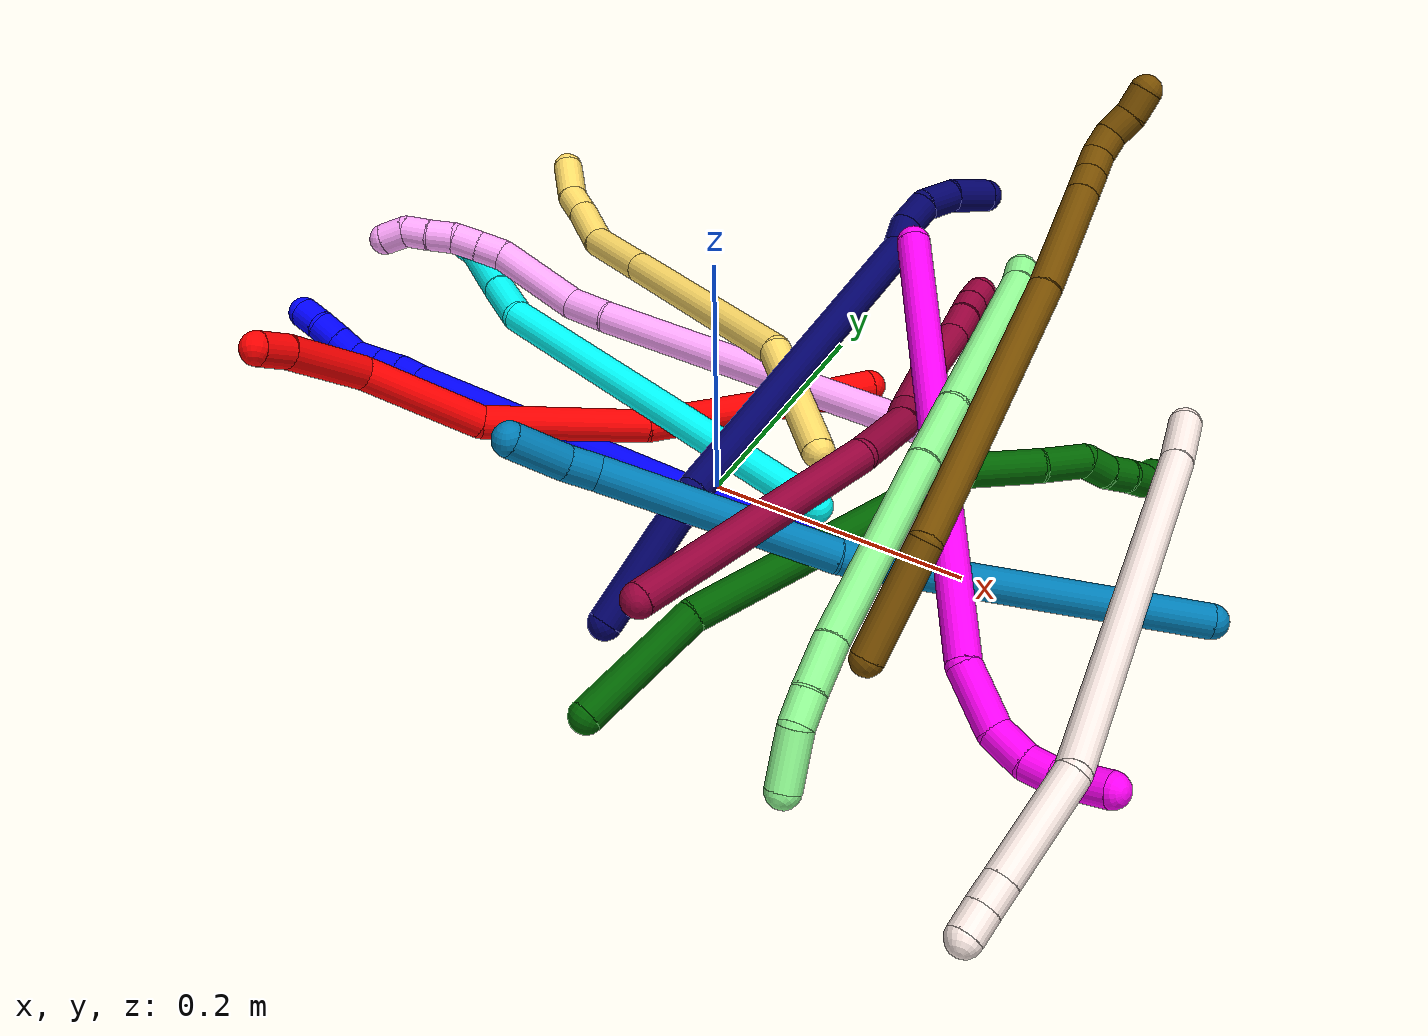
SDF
<sdf version="1.7">
 <world name="default">
  <plugin name="TubeGeneratorPlugin" filename="libtube_generator_plugin.so"/>
  <model name="photoneo_s_sensor">
   <static>1</static>
   <pose>0 0 2 1.57079 1.57079 3.14159</pose>
   <link name="link">
    <inertial><mass>0.1</mass></inertial>
    <sensor name="sensor" type="depth">
     <update_rate>30</update_rate>
     <camera>
      <horizontal_fov>1.22</horizontal_fov>
      <image><width>1920</width><height>1200</height><format>B8G8R8</format></image>
      <clip><near>0.1</near><far>4</far></clip>
      <depth_camera><output>points</output></depth_camera>
     </camera>
     <plugin name="camera_plugin" filename="libgazebo_ros_depth_camera.so">
      <baseline>0.2</baseline>
      <alwaysOn>1</alwaysOn>
      <updateRate>0.0</updateRate>
      <cameraName>camera_ir</cameraName>
      <imageTopicName>/camera/color/image_raw</imageTopicName>
      <cameraInfoTopicName>/camera/color/camera_info</cameraInfoTopicName>
      <depthImageTopicName>/camera/depth/image_raw</depthImageTopicName>
      <depthImageCameraInfoTopicName>/camera/depth/camera_info</depthImageCameraInfoTopicName>
      <pointCloudTopicName>/camera/depth/points</pointCloudTopicName>
      <frameName>fr_optical</frameName>
      <pointCloudCutoff>0.1</pointCloudCutoff>
      <pointCloudCutoffMax>2.0</pointCloudCutoffMax>
      <distortionK1>0</distortionK1>
      <distortionK2>0</distortionK2>
      <distortionK3>0</distortionK3>
      <distortionT1>0</distortionT1>
      <distortionT2>0</distortionT2>
      <CxPrime>0</CxPrime>
      <Cx>0</Cx>
      <Cy>0</Cy>
      <focalLength>0</focalLength>
      <hackBaseline>0</hackBaseline>
     </plugin>
    </sensor>
   </link>
  </model>
  <gravity>0 0 -9.8</gravity>
  <magnetic_field>6e-06 2.3e-05 -4.2e-05</magnetic_field>
  <atmosphere type="adiabatic"/>
  <physics name="default_physics" default="0" type="ode">
   <max_step_size>0.003</max_step_size>
   <real_time_factor>1</real_time_factor>
   <real_time_update_rate>1000</real_time_update_rate>
   <max_contacts>10000</max_contacts>
   <ode>
    <solver>
     <type>quick</type>
     <iters>100</iters>
     <sor>1.3</sor>
     <use_dynamic_moi_rescaling>0</use_dynamic_moi_rescaling>
    </solver>
    <constraints>
     <contact_max_correcting_vel>0</contact_max_correcting_vel>
     <contact_surface_layer>0.001</contact_surface_layer>
     <cfm>0</cfm>
     <erp>0.2</erp>
    </constraints>
   </ode>
  </physics>
  <scene><ambient>0.4 0.4 0.4 1</ambient><background>0.7 0.7 0.7 1</background><shadows>0</shadows></scene>
  <audio><device>default</device></audio>
  <spherical_coordinates>
   <surface_model>EARTH_WGS84</surface_model>
   <latitude_deg>0</latitude_deg>
   <longitude_deg>0</longitude_deg>
   <elevation>0</elevation>
   <heading_deg>0</heading_deg>
  </spherical_coordinates>
  <model name="bin">
   <static>1</static>
   <link name="bottom">
    <collision name="collision-bottom">
     <pose>0 0 -0.01 0 -0 0</pose>
     <geometry><box><size>0.8 0.6 0.02</size></box></geometry>
     <surface>
      <friction><ode><mu>100</mu><mu2>100</mu2></ode></friction>
      <contact><collide_bitmask>65535</collide_bitmask></contact>
     </surface>
    </collision>
   </link>
   <link name="west_wall">
    <collision name="collision-west_wall">
     <pose>-0.41 0 0.1 0 -0 0</pose>
     <geometry><box><size>0.02 0.6 0.2</size></box></geometry>
     <surface>
      <friction><ode><mu>100</mu><mu2>100</mu2></ode></friction>
      <contact><collide_bitmask>65535</collide_bitmask></contact>
     </surface>
    </collision>
   </link>
   <link name="east_wall">
    <collision name="collision-east_wall">
     <pose>0.41 0 0.1 0 -0 0</pose>
     <geometry><box><size>0.02 0.6 0.2</size></box></geometry>
     <surface>
      <friction><ode><mu>100</mu><mu2>100</mu2></ode></friction>
      <contact><collide_bitmask>65535</collide_bitmask></contact>
     </surface>
    </collision>
   </link>
   <link name="south_wall">
    <collision name="collision-south_wall">
     <pose>0 -0.31 0.1 0 -0 0</pose>
     <geometry><box><size>0.8 0.02 0.2</size></box></geometry>
     <surface>
      <friction><ode><mu>100</mu><mu2>100</mu2></ode></friction>
      <contact><collide_bitmask>65535</collide_bitmask></contact>
     </surface>
    </collision>
   </link>
   <link name="north_wall">
    <collision name="collision-north_wall">
     <pose>0 0.31 0.1 0 -0 0</pose>
     <geometry><box><size>0.8 0.02 0.2</size></box></geometry>
     <surface>
      <friction><ode><mu>100</mu><mu2>100</mu2></ode></friction>
      <contact><collide_bitmask>65535</collide_bitmask></contact>
     </surface>
    </collision>
   </link>
  </model>
  <model name="1">
   <static>0</static>
   <link name="1">
    <collision name="collision-cylinder-e_1_1_4">
     <pose>-0.186642 -0.009663 -0.02153 2.71971 -1.44502 -2.66501</pose>
     <geometry><cylinder><radius>0.0125</radius><length>0.376257</length></cylinder></geometry>
     <surface>
      <friction><ode><mu>1.16</mu><mu2>1.16</mu2><slip1>0</slip1><slip2>0</slip2></ode></friction>
      <contact><ode><kp>1e+06</kp><kd>1</kd><max_vel>0</max_vel><min_depth>0.001</min_depth></ode></contact>
     </surface>
    </collision>
    <visual name="visual-cylinder-e_1_1_4">
     <pose>-0.186642 -0.009663 -0.02153 2.71971 -1.44502 -2.66501</pose>
     <geometry><cylinder><radius>0.0125</radius><length>0.376257</length></cylinder></geometry>
     <material><ambient>0 0 1 1</ambient></material>
    </visual>
    <collision name="collision-cylinder-e_2_4_5">
     <pose>-0.383869 -0.019695 -0.044904 2.94471 -1.39492 -2.90695</pose>
     <geometry><cylinder><radius>0.0125</radius><length>0.0215</length></cylinder></geometry>
     <surface>
      <friction><ode><mu>1.16</mu><mu2>1.16</mu2><slip1>0</slip1><slip2>0</slip2></ode></friction>
      <contact><ode><kp>1e+06</kp><kd>1</kd><max_vel>0</max_vel><min_depth>0.001</min_depth></ode></contact>
     </surface>
    </collision>
    <visual name="visual-cylinder-e_2_4_5">
     <pose>-0.383869 -0.019695 -0.044904 2.94471 -1.39492 -2.90695</pose>
     <geometry><cylinder><radius>0.0125</radius><length>0.0215</length></cylinder></geometry>
     <material><ambient>0 0 1 1</ambient></material>
    </visual>
    <collision name="collision-cylinder-e_3_5_6">
     <pose>-0.404504 -0.020289 -0.046749 1.57332 -1.5483 -1.55082</pose>
     <geometry><cylinder><radius>0.0125</radius><length>0.020106</length></cylinder></geometry>
     <surface>
      <friction><ode><mu>1.16</mu><mu2>1.16</mu2><slip1>0</slip1><slip2>0</slip2></ode></friction>
      <contact><ode><kp>1e+06</kp><kd>1</kd><max_vel>0</max_vel><min_depth>0.001</min_depth></ode></contact>
     </surface>
    </collision>
    <visual name="visual-cylinder-e_3_5_6">
     <pose>-0.404504 -0.020289 -0.046749 1.57332 -1.5483 -1.55082</pose>
     <geometry><cylinder><radius>0.0125</radius><length>0.020106</length></cylinder></geometry>
     <material><ambient>0 0 1 1</ambient></material>
    </visual>
    <collision name="collision-cylinder-e_4_6_7">
     <pose>-0.425304 -0.020434 -0.046728 -1.30361 -1.56296 1.29606</pose>
     <geometry><cylinder><radius>0.0125</radius><length>0.021501</length></cylinder></geometry>
     <surface>
      <friction><ode><mu>1.16</mu><mu2>1.16</mu2><slip1>0</slip1><slip2>0</slip2></ode></friction>
      <contact><ode><kp>1e+06</kp><kd>1</kd><max_vel>0</max_vel><min_depth>0.001</min_depth></ode></contact>
     </surface>
    </collision>
    <visual name="visual-cylinder-e_4_6_7">
     <pose>-0.425304 -0.020434 -0.046728 -1.30361 -1.56296 1.29606</pose>
     <geometry><cylinder><radius>0.0125</radius><length>0.021501</length></cylinder></geometry>
     <material><ambient>0 0 1 1</ambient></material>
    </visual>
    <collision name="collision-cylinder-e_5_7_8">
     <pose>-0.445386 -0.017454 -0.049272 -2.29549 -1.17752 1.95512</pose>
     <geometry><cylinder><radius>0.0125</radius><length>0.020206</length></cylinder></geometry>
     <surface>
      <friction><ode><mu>1.16</mu><mu2>1.16</mu2><slip1>0</slip1><slip2>0</slip2></ode></friction>
      <contact><ode><kp>1e+06</kp><kd>1</kd><max_vel>0</max_vel><min_depth>0.001</min_depth></ode></contact>
     </surface>
    </collision>
    <visual name="visual-cylinder-e_5_7_8">
     <pose>-0.445386 -0.017454 -0.049272 -2.29549 -1.17752 1.95512</pose>
     <geometry><cylinder><radius>0.0125</radius><length>0.020206</length></cylinder></geometry>
     <material><ambient>0 0 1 1</ambient></material>
    </visual>
    <collision name="collision-cylinder-e_6_8_9">
     <pose>-0.464091 -0.011868 -0.054175 -2.28645 -1.20775 1.97406</pose>
     <geometry><cylinder><radius>0.0125</radius><length>0.020054</length></cylinder></geometry>
     <surface>
      <friction><ode><mu>1.16</mu><mu2>1.16</mu2><slip1>0</slip1><slip2>0</slip2></ode></friction>
      <contact><ode><kp>1e+06</kp><kd>1</kd><max_vel>0</max_vel><min_depth>0.001</min_depth></ode></contact>
     </surface>
    </collision>
    <visual name="visual-cylinder-e_6_8_9">
     <pose>-0.464091 -0.011868 -0.054175 -2.28645 -1.20775 1.97406</pose>
     <geometry><cylinder><radius>0.0125</radius><length>0.020054</length></cylinder></geometry>
     <material><ambient>0 0 1 1</ambient></material>
    </visual>
    <collision name="collision-cylinder-e_7_9_2">
     <pose>-0.483127 -0.008779 -0.059719 -3.01712 -1.24792 2.9689</pose>
     <geometry><cylinder><radius>0.0125</radius><length>0.020376</length></cylinder></geometry>
     <surface>
      <friction><ode><mu>1.16</mu><mu2>1.16</mu2><slip1>0</slip1><slip2>0</slip2></ode></friction>
      <contact><ode><kp>1e+06</kp><kd>1</kd><max_vel>0</max_vel><min_depth>0.001</min_depth></ode></contact>
     </surface>
    </collision>
    <visual name="visual-cylinder-e_7_9_2">
     <pose>-0.483127 -0.008779 -0.059719 -3.01712 -1.24792 2.9689</pose>
     <geometry><cylinder><radius>0.0125</radius><length>0.020376</length></cylinder></geometry>
     <material><ambient>0 0 1 1</ambient></material>
    </visual>
    <collision name="collision-sphere-2">
     <pose>-0.492788 -0.008378 -0.062926 0 -0 0</pose>
     <geometry><sphere><radius>0.0125</radius></sphere></geometry>
     <surface>
      <friction><ode><mu>1.16</mu><mu2>1.16</mu2><slip1>0</slip1><slip2>0</slip2></ode></friction>
      <contact><ode><kp>1e+06</kp><kd>1</kd><max_vel>0</max_vel><min_depth>0.001</min_depth></ode></contact>
     </surface>
    </collision>
    <visual name="visual-sphere-2">
     <pose>-0.492788 -0.008378 -0.062926 0 -0 0</pose>
     <geometry><sphere><radius>0.0125</radius></sphere></geometry>
     <material><ambient>0 0 1 1</ambient></material>
    </visual>
    <collision name="collision-sphere-9">
     <pose>-0.473465 -0.009181 -0.056511 0 -0 0</pose>
     <geometry><sphere><radius>0.0125</radius></sphere></geometry>
     <surface>
      <friction><ode><mu>1.16</mu><mu2>1.16</mu2><slip1>0</slip1><slip2>0</slip2></ode></friction>
      <contact><ode><kp>1e+06</kp><kd>1</kd><max_vel>0</max_vel><min_depth>0.001</min_depth></ode></contact>
     </surface>
    </collision>
    <visual name="visual-sphere-9">
     <pose>-0.473465 -0.009181 -0.056511 0 -0 0</pose>
     <geometry><sphere><radius>0.0125</radius></sphere></geometry>
     <material><ambient>0 0 1 1</ambient></material>
    </visual>
    <collision name="collision-sphere-4">
     <pose>-0.373285 -0.019327 -0.04306 0 -0 0</pose>
     <geometry><sphere><radius>0.0125</radius></sphere></geometry>
     <surface>
      <friction><ode><mu>1.16</mu><mu2>1.16</mu2><slip1>0</slip1><slip2>0</slip2></ode></friction>
      <contact><ode><kp>1e+06</kp><kd>1</kd><max_vel>0</max_vel><min_depth>0.001</min_depth></ode></contact>
     </surface>
    </collision>
    <visual name="visual-sphere-4">
     <pose>-0.373285 -0.019327 -0.04306 0 -0 0</pose>
     <geometry><sphere><radius>0.0125</radius></sphere></geometry>
     <material><ambient>0 0 1 1</ambient></material>
    </visual>
    <collision name="collision-sphere-1">
     <geometry><sphere><radius>0.0125</radius></sphere></geometry>
     <surface>
      <friction><ode><mu>1.16</mu><mu2>1.16</mu2><slip1>0</slip1><slip2>0</slip2></ode></friction>
      <contact><ode><kp>1e+06</kp><kd>1</kd><max_vel>0</max_vel><min_depth>0.001</min_depth></ode></contact>
     </surface>
    </collision>
    <visual name="visual-sphere-1">
     <geometry><sphere><radius>0.0125</radius></sphere></geometry>
     <material><ambient>0 0 1 1</ambient></material>
    </visual>
    <collision name="collision-sphere-8">
     <pose>-0.454718 -0.014555 -0.051838 0 -0 0</pose>
     <geometry><sphere><radius>0.0125</radius></sphere></geometry>
     <surface>
      <friction><ode><mu>1.16</mu><mu2>1.16</mu2><slip1>0</slip1><slip2>0</slip2></ode></friction>
      <contact><ode><kp>1e+06</kp><kd>1</kd><max_vel>0</max_vel><min_depth>0.001</min_depth></ode></contact>
     </surface>
    </collision>
    <visual name="visual-sphere-8">
     <pose>-0.454718 -0.014555 -0.051838 0 -0 0</pose>
     <geometry><sphere><radius>0.0125</radius></sphere></geometry>
     <material><ambient>0 0 1 1</ambient></material>
    </visual>
    <collision name="collision-sphere-5">
     <pose>-0.394453 -0.020063 -0.046749 0 -0 0</pose>
     <geometry><sphere><radius>0.0125</radius></sphere></geometry>
     <surface>
      <friction><ode><mu>1.16</mu><mu2>1.16</mu2><slip1>0</slip1><slip2>0</slip2></ode></friction>
      <contact><ode><kp>1e+06</kp><kd>1</kd><max_vel>0</max_vel><min_depth>0.001</min_depth></ode></contact>
     </surface>
    </collision>
    <visual name="visual-sphere-5">
     <pose>-0.394453 -0.020063 -0.046749 0 -0 0</pose>
     <geometry><sphere><radius>0.0125</radius></sphere></geometry>
     <material><ambient>0 0 1 1</ambient></material>
    </visual>
    <collision name="collision-sphere-6">
     <pose>-0.414554 -0.020515 -0.04675 0 -0 0</pose>
     <geometry><sphere><radius>0.0125</radius></sphere></geometry>
     <surface>
      <friction><ode><mu>1.16</mu><mu2>1.16</mu2><slip1>0</slip1><slip2>0</slip2></ode></friction>
      <contact><ode><kp>1e+06</kp><kd>1</kd><max_vel>0</max_vel><min_depth>0.001</min_depth></ode></contact>
     </surface>
    </collision>
    <visual name="visual-sphere-6">
     <pose>-0.414554 -0.020515 -0.04675 0 -0 0</pose>
     <geometry><sphere><radius>0.0125</radius></sphere></geometry>
     <material><ambient>0 0 1 1</ambient></material>
    </visual>
    <collision name="collision-sphere-7">
     <pose>-0.436055 -0.020352 -0.046705 0 -0 0</pose>
     <geometry><sphere><radius>0.0125</radius></sphere></geometry>
     <surface>
      <friction><ode><mu>1.16</mu><mu2>1.16</mu2><slip1>0</slip1><slip2>0</slip2></ode></friction>
      <contact><ode><kp>1e+06</kp><kd>1</kd><max_vel>0</max_vel><min_depth>0.001</min_depth></ode></contact>
     </surface>
    </collision>
    <visual name="visual-sphere-7">
     <pose>-0.436055 -0.020352 -0.046705 0 -0 0</pose>
     <geometry><sphere><radius>0.0125</radius></sphere></geometry>
     <material><ambient>0 0 1 1</ambient></material>
    </visual>
    <inertial>
     <pose>-0.247813 -0.011352 -0.028619 0 -0 0</pose>
     <mass>0.5</mass>
     <inertia>
      <ixx>-0.000791</ixx>
      <ixy>0</ixy>
      <ixz>0</ixz>
      <iyy>0.004193</iyy>
      <iyz>0</iyz>
      <izz>0.00465</izz>
     </inertia>
    </inertial>
   </link>
   <pose>0.116482 -0.031723 0.011495 1.71848 0.034331 0.084768</pose>
  </model>
  <model name="2">
   <static>0</static>
   <link name="2">
    <collision name="collision-cylinder-e_1_1_4">
     <pose>-0.018717 -0.014627 0.008482 1.0453 -0.836107 -0.501084</pose>
     <geometry><cylinder><radius>0.0125</radius><length>0.050447</length></cylinder></geometry>
     <surface>
      <friction><ode><mu>1.16</mu><mu2>1.16</mu2><slip1>0</slip1><slip2>0</slip2></ode></friction>
      <contact><ode><kp>1e+06</kp><kd>1</kd><max_vel>0</max_vel><min_depth>0.001</min_depth></ode></contact>
     </surface>
    </collision>
    <visual name="visual-cylinder-e_1_1_4">
     <pose>-0.018717 -0.014627 0.008482 1.0453 -0.836107 -0.501084</pose>
     <geometry><cylinder><radius>0.0125</radius><length>0.050447</length></cylinder></geometry>
     <material><ambient>1 0 0 1</ambient></material>
    </visual>
    <collision name="collision-cylinder-e_2_4_5">
     <pose>-0.088711 -0.067973 0.037568 1.08176 -0.863214 -0.539759</pose>
     <geometry><cylinder><radius>0.0125</radius><length>0.134952</length></cylinder></geometry>
     <surface>
      <friction><ode><mu>1.16</mu><mu2>1.16</mu2><slip1>0</slip1><slip2>0</slip2></ode></friction>
      <contact><ode><kp>1e+06</kp><kd>1</kd><max_vel>0</max_vel><min_depth>0.001</min_depth></ode></contact>
     </surface>
    </collision>
    <visual name="visual-cylinder-e_2_4_5">
     <pose>-0.088711 -0.067973 0.037568 1.08176 -0.863214 -0.539759</pose>
     <geometry><cylinder><radius>0.0125</radius><length>0.134952</length></cylinder></geometry>
     <material><ambient>1 0 0 1</ambient></material>
    </visual>
    <collision name="collision-cylinder-e_3_5_6">
     <pose>-0.192421 -0.14106 0.066809 1.3246 -0.976448 -0.785302</pose>
     <geometry><cylinder><radius>0.0125</radius><length>0.126572</length></cylinder></geometry>
     <surface>
      <friction><ode><mu>1.16</mu><mu2>1.16</mu2><slip1>0</slip1><slip2>0</slip2></ode></friction>
      <contact><ode><kp>1e+06</kp><kd>1</kd><max_vel>0</max_vel><min_depth>0.001</min_depth></ode></contact>
     </surface>
    </collision>
    <visual name="visual-cylinder-e_3_5_6">
     <pose>-0.192421 -0.14106 0.066809 1.3246 -0.976448 -0.785302</pose>
     <geometry><cylinder><radius>0.0125</radius><length>0.126572</length></cylinder></geometry>
     <material><ambient>1 0 0 1</ambient></material>
    </visual>
    <collision name="collision-cylinder-e_4_6_7">
     <pose>-0.288249 -0.19157 0.068105 1.99765 -1.18289 -1.61321</pose>
     <geometry><cylinder><radius>0.0125</radius><length>0.093754</length></cylinder></geometry>
     <surface>
      <friction><ode><mu>1.16</mu><mu2>1.16</mu2><slip1>0</slip1><slip2>0</slip2></ode></friction>
      <contact><ode><kp>1e+06</kp><kd>1</kd><max_vel>0</max_vel><min_depth>0.001</min_depth></ode></contact>
     </surface>
    </collision>
    <visual name="visual-cylinder-e_4_6_7">
     <pose>-0.288249 -0.19157 0.068105 1.99765 -1.18289 -1.61321</pose>
     <geometry><cylinder><radius>0.0125</radius><length>0.093754</length></cylinder></geometry>
     <material><ambient>1 0 0 1</ambient></material>
    </visual>
    <collision name="collision-cylinder-e_5_7_8">
     <pose>-0.365581 -0.207243 0.066663 -0.079081 -1.39817 0.066495</pose>
     <geometry><cylinder><radius>0.0125</radius><length>0.068901</length></cylinder></geometry>
     <surface>
      <friction><ode><mu>1.16</mu><mu2>1.16</mu2><slip1>0</slip1><slip2>0</slip2></ode></friction>
      <contact><ode><kp>1e+06</kp><kd>1</kd><max_vel>0</max_vel><min_depth>0.001</min_depth></ode></contact>
     </surface>
    </collision>
    <visual name="visual-cylinder-e_5_7_8">
     <pose>-0.365581 -0.207243 0.066663 -0.079081 -1.39817 0.066495</pose>
     <geometry><cylinder><radius>0.0125</radius><length>0.068901</length></cylinder></geometry>
     <material><ambient>1 0 0 1</ambient></material>
    </visual>
    <collision name="collision-cylinder-e_6_8_2">
     <pose>-0.411651 -0.207368 0.076231 0.160038 -1.27354 -0.118468</pose>
     <geometry><cylinder><radius>0.0125</radius><length>0.025375</length></cylinder></geometry>
     <surface>
      <friction><ode><mu>1.16</mu><mu2>1.16</mu2><slip1>0</slip1><slip2>0</slip2></ode></friction>
      <contact><ode><kp>1e+06</kp><kd>1</kd><max_vel>0</max_vel><min_depth>0.001</min_depth></ode></contact>
     </surface>
    </collision>
    <visual name="visual-cylinder-e_6_8_2">
     <pose>-0.411651 -0.207368 0.076231 0.160038 -1.27354 -0.118468</pose>
     <geometry><cylinder><radius>0.0125</radius><length>0.025375</length></cylinder></geometry>
     <material><ambient>1 0 0 1</ambient></material>
    </visual>
    <collision name="collision-sphere-2">
     <pose>-0.423782 -0.20796 0.0799 0 -0 0</pose>
     <geometry><sphere><radius>0.0125</radius></sphere></geometry>
     <surface>
      <friction><ode><mu>1.16</mu><mu2>1.16</mu2><slip1>0</slip1><slip2>0</slip2></ode></friction>
      <contact><ode><kp>1e+06</kp><kd>1</kd><max_vel>0</max_vel><min_depth>0.001</min_depth></ode></contact>
     </surface>
    </collision>
    <visual name="visual-sphere-2">
     <pose>-0.423782 -0.20796 0.0799 0 -0 0</pose>
     <geometry><sphere><radius>0.0125</radius></sphere></geometry>
     <material><ambient>1 0 0 1</ambient></material>
    </visual>
    <collision name="collision-sphere-4">
     <pose>-0.037434 -0.029254 0.016964 0 -0 0</pose>
     <geometry><sphere><radius>0.0125</radius></sphere></geometry>
     <surface>
      <friction><ode><mu>1.16</mu><mu2>1.16</mu2><slip1>0</slip1><slip2>0</slip2></ode></friction>
      <contact><ode><kp>1e+06</kp><kd>1</kd><max_vel>0</max_vel><min_depth>0.001</min_depth></ode></contact>
     </surface>
    </collision>
    <visual name="visual-sphere-4">
     <pose>-0.037434 -0.029254 0.016964 0 -0 0</pose>
     <geometry><sphere><radius>0.0125</radius></sphere></geometry>
     <material><ambient>1 0 0 1</ambient></material>
    </visual>
    <collision name="collision-sphere-1">
     <geometry><sphere><radius>0.0125</radius></sphere></geometry>
     <surface>
      <friction><ode><mu>1.16</mu><mu2>1.16</mu2><slip1>0</slip1><slip2>0</slip2></ode></friction>
      <contact><ode><kp>1e+06</kp><kd>1</kd><max_vel>0</max_vel><min_depth>0.001</min_depth></ode></contact>
     </surface>
    </collision>
    <visual name="visual-sphere-1">
     <geometry><sphere><radius>0.0125</radius></sphere></geometry>
     <material><ambient>1 0 0 1</ambient></material>
    </visual>
    <collision name="collision-sphere-8">
     <pose>-0.39952 -0.206775 0.072563 0 -0 0</pose>
     <geometry><sphere><radius>0.0125</radius></sphere></geometry>
     <surface>
      <friction><ode><mu>1.16</mu><mu2>1.16</mu2><slip1>0</slip1><slip2>0</slip2></ode></friction>
      <contact><ode><kp>1e+06</kp><kd>1</kd><max_vel>0</max_vel><min_depth>0.001</min_depth></ode></contact>
     </surface>
    </collision>
    <visual name="visual-sphere-8">
     <pose>-0.39952 -0.206775 0.072563 0 -0 0</pose>
     <geometry><sphere><radius>0.0125</radius></sphere></geometry>
     <material><ambient>1 0 0 1</ambient></material>
    </visual>
    <collision name="collision-sphere-5">
     <pose>-0.139988 -0.106691 0.058172 0 -0 0</pose>
     <geometry><sphere><radius>0.0125</radius></sphere></geometry>
     <surface>
      <friction><ode><mu>1.16</mu><mu2>1.16</mu2><slip1>0</slip1><slip2>0</slip2></ode></friction>
      <contact><ode><kp>1e+06</kp><kd>1</kd><max_vel>0</max_vel><min_depth>0.001</min_depth></ode></contact>
     </surface>
    </collision>
    <visual name="visual-sphere-5">
     <pose>-0.139988 -0.106691 0.058172 0 -0 0</pose>
     <geometry><sphere><radius>0.0125</radius></sphere></geometry>
     <material><ambient>1 0 0 1</ambient></material>
    </visual>
    <collision name="collision-sphere-6">
     <pose>-0.244854 -0.17543 0.075446 0 -0 0</pose>
     <geometry><sphere><radius>0.0125</radius></sphere></geometry>
     <surface>
      <friction><ode><mu>1.16</mu><mu2>1.16</mu2><slip1>0</slip1><slip2>0</slip2></ode></friction>
      <contact><ode><kp>1e+06</kp><kd>1</kd><max_vel>0</max_vel><min_depth>0.001</min_depth></ode></contact>
     </surface>
    </collision>
    <visual name="visual-sphere-6">
     <pose>-0.244854 -0.17543 0.075446 0 -0 0</pose>
     <geometry><sphere><radius>0.0125</radius></sphere></geometry>
     <material><ambient>1 0 0 1</ambient></material>
    </visual>
    <collision name="collision-sphere-7">
     <pose>-0.331643 -0.20771 0.060764 0 -0 0</pose>
     <geometry><sphere><radius>0.0125</radius></sphere></geometry>
     <surface>
      <friction><ode><mu>1.16</mu><mu2>1.16</mu2><slip1>0</slip1><slip2>0</slip2></ode></friction>
      <contact><ode><kp>1e+06</kp><kd>1</kd><max_vel>0</max_vel><min_depth>0.001</min_depth></ode></contact>
     </surface>
    </collision>
    <visual name="visual-sphere-7">
     <pose>-0.331643 -0.20771 0.060764 0 -0 0</pose>
     <geometry><sphere><radius>0.0125</radius></sphere></geometry>
     <material><ambient>1 0 0 1</ambient></material>
    </visual>
    <inertial>
     <pose>-0.19986 -0.130534 0.053733 0 -0 0</pose>
     <mass>0.5</mass>
     <inertia><ixx>-5e-06</ixx><ixy>0</ixy><ixz>0</ixz><iyy>0.000203</iyy><iyz>0</iyz><izz>0.000665</izz></inertia>
    </inertial>
   </link>
   <pose>0.049699 0.151118 0.011488 2.22008 0.789616 0.991381</pose>
  </model>
  <model name="3">
   <static>0</static>
   <link name="3">
    <collision name="collision-cylinder-e_1_1_4">
     <pose>-0.082379 0.137709 0.018798 -1.43513 -0.535045 0.469613</pose>
     <geometry><cylinder><radius>0.0125</radius><length>0.323132</length></cylinder></geometry>
     <surface>
      <friction><ode><mu>1.16</mu><mu2>1.16</mu2><slip1>0</slip1><slip2>0</slip2></ode></friction>
      <contact><ode><kp>1e+06</kp><kd>1</kd><max_vel>0</max_vel><min_depth>0.001</min_depth></ode></contact>
     </surface>
    </collision>
    <visual name="visual-cylinder-e_1_1_4">
     <pose>-0.082379 0.137709 0.018798 -1.43513 -0.535045 0.469613</pose>
     <geometry><cylinder><radius>0.0125</radius><length>0.323132</length></cylinder></geometry>
     <material><ambient>0.003922 1 0.996078 1</ambient></material>
    </visual>
    <collision name="collision-cylinder-e_2_4_5">
     <pose>-0.182928 0.289338 0.043498 -1.16978 -0.876811 0.602039</pose>
     <geometry><cylinder><radius>0.0125</radius><length>0.047274</length></cylinder></geometry>
     <surface>
      <friction><ode><mu>1.16</mu><mu2>1.16</mu2><slip1>0</slip1><slip2>0</slip2></ode></friction>
      <contact><ode><kp>1e+06</kp><kd>1</kd><max_vel>0</max_vel><min_depth>0.001</min_depth></ode></contact>
     </surface>
    </collision>
    <visual name="visual-cylinder-e_2_4_5">
     <pose>-0.182928 0.289338 0.043498 -1.16978 -0.876811 0.602039</pose>
     <geometry><cylinder><radius>0.0125</radius><length>0.047274</length></cylinder></geometry>
     <material><ambient>0.003922 1 0.996078 1</ambient></material>
    </visual>
    <collision name="collision-cylinder-e_3_5_6">
     <pose>-0.233121 0.325754 0.061758 -1.06846 -0.895108 0.553426</pose>
     <geometry><cylinder><radius>0.0125</radius><length>0.082081</length></cylinder></geometry>
     <surface>
      <friction><ode><mu>1.16</mu><mu2>1.16</mu2><slip1>0</slip1><slip2>0</slip2></ode></friction>
      <contact><ode><kp>1e+06</kp><kd>1</kd><max_vel>0</max_vel><min_depth>0.001</min_depth></ode></contact>
     </surface>
    </collision>
    <visual name="visual-cylinder-e_3_5_6">
     <pose>-0.233121 0.325754 0.061758 -1.06846 -0.895108 0.553426</pose>
     <geometry><cylinder><radius>0.0125</radius><length>0.082081</length></cylinder></geometry>
     <material><ambient>0.003922 1 0.996078 1</ambient></material>
    </visual>
    <collision name="collision-cylinder-e_4_6_7">
     <pose>-0.272664 0.354936 0.079731 -0.872324 -0.711039 0.342728</pose>
     <geometry><cylinder><radius>0.0125</radius><length>0.023043</length></cylinder></geometry>
     <surface>
      <friction><ode><mu>1.16</mu><mu2>1.16</mu2><slip1>0</slip1><slip2>0</slip2></ode></friction>
      <contact><ode><kp>1e+06</kp><kd>1</kd><max_vel>0</max_vel><min_depth>0.001</min_depth></ode></contact>
     </surface>
    </collision>
    <visual name="visual-cylinder-e_4_6_7">
     <pose>-0.272664 0.354936 0.079731 -0.872324 -0.711039 0.342728</pose>
     <geometry><cylinder><radius>0.0125</radius><length>0.023043</length></cylinder></geometry>
     <material><ambient>0.003922 1 0.996078 1</ambient></material>
    </visual>
    <collision name="collision-cylinder-e_5_7_2">
     <pose>-0.289534 0.366596 0.091469 -0.682169 -0.869934 0.326917</pose>
     <geometry><cylinder><radius>0.0125</radius><length>0.024469</length></cylinder></geometry>
     <surface>
      <friction><ode><mu>1.16</mu><mu2>1.16</mu2><slip1>0</slip1><slip2>0</slip2></ode></friction>
      <contact><ode><kp>1e+06</kp><kd>1</kd><max_vel>0</max_vel><min_depth>0.001</min_depth></ode></contact>
     </surface>
    </collision>
    <visual name="visual-cylinder-e_5_7_2">
     <pose>-0.289534 0.366596 0.091469 -0.682169 -0.869934 0.326917</pose>
     <geometry><cylinder><radius>0.0125</radius><length>0.024469</length></cylinder></geometry>
     <material><ambient>0.003922 1 0.996078 1</ambient></material>
    </visual>
    <collision name="collision-sphere-2">
     <pose>-0.298884 0.371571 0.097593 0 -0 0</pose>
     <geometry><sphere><radius>0.0125</radius></sphere></geometry>
     <surface>
      <friction><ode><mu>1.16</mu><mu2>1.16</mu2><slip1>0</slip1><slip2>0</slip2></ode></friction>
      <contact><ode><kp>1e+06</kp><kd>1</kd><max_vel>0</max_vel><min_depth>0.001</min_depth></ode></contact>
     </surface>
    </collision>
    <visual name="visual-sphere-2">
     <pose>-0.298884 0.371571 0.097593 0 -0 0</pose>
     <geometry><sphere><radius>0.0125</radius></sphere></geometry>
     <material><ambient>0.003922 1 0.996078 1</ambient></material>
    </visual>
    <collision name="collision-sphere-7">
     <pose>-0.280183 0.361622 0.085344 0 -0 0</pose>
     <geometry><sphere><radius>0.0125</radius></sphere></geometry>
     <surface>
      <friction><ode><mu>1.16</mu><mu2>1.16</mu2><slip1>0</slip1><slip2>0</slip2></ode></friction>
      <contact><ode><kp>1e+06</kp><kd>1</kd><max_vel>0</max_vel><min_depth>0.001</min_depth></ode></contact>
     </surface>
    </collision>
    <visual name="visual-sphere-7">
     <pose>-0.280183 0.361622 0.085344 0 -0 0</pose>
     <geometry><sphere><radius>0.0125</radius></sphere></geometry>
     <material><ambient>0.003922 1 0.996078 1</ambient></material>
    </visual>
    <collision name="collision-sphere-6">
     <pose>-0.265144 0.348251 0.074117 0 -0 0</pose>
     <geometry><sphere><radius>0.0125</radius></sphere></geometry>
     <surface>
      <friction><ode><mu>1.16</mu><mu2>1.16</mu2><slip1>0</slip1><slip2>0</slip2></ode></friction>
      <contact><ode><kp>1e+06</kp><kd>1</kd><max_vel>0</max_vel><min_depth>0.001</min_depth></ode></contact>
     </surface>
    </collision>
    <visual name="visual-sphere-6">
     <pose>-0.265144 0.348251 0.074117 0 -0 0</pose>
     <geometry><sphere><radius>0.0125</radius></sphere></geometry>
     <material><ambient>0.003922 1 0.996078 1</ambient></material>
    </visual>
    <collision name="collision-sphere-5">
     <pose>-0.201098 0.303257 0.0494 0 -0 0</pose>
     <geometry><sphere><radius>0.0125</radius></sphere></geometry>
     <surface>
      <friction><ode><mu>1.16</mu><mu2>1.16</mu2><slip1>0</slip1><slip2>0</slip2></ode></friction>
      <contact><ode><kp>1e+06</kp><kd>1</kd><max_vel>0</max_vel><min_depth>0.001</min_depth></ode></contact>
     </surface>
    </collision>
    <visual name="visual-sphere-5">
     <pose>-0.201098 0.303257 0.0494 0 -0 0</pose>
     <geometry><sphere><radius>0.0125</radius></sphere></geometry>
     <material><ambient>0.003922 1 0.996078 1</ambient></material>
    </visual>
    <collision name="collision-sphere-1">
     <geometry><sphere><radius>0.0125</radius></sphere></geometry>
     <surface>
      <friction><ode><mu>1.16</mu><mu2>1.16</mu2><slip1>0</slip1><slip2>0</slip2></ode></friction>
      <contact><ode><kp>1e+06</kp><kd>1</kd><max_vel>0</max_vel><min_depth>0.001</min_depth></ode></contact>
     </surface>
    </collision>
    <visual name="visual-sphere-1">
     <geometry><sphere><radius>0.0125</radius></sphere></geometry>
     <material><ambient>0.003922 1 0.996078 1</ambient></material>
    </visual>
    <collision name="collision-sphere-4">
     <pose>-0.164759 0.275419 0.037597 0 -0 0</pose>
     <geometry><sphere><radius>0.0125</radius></sphere></geometry>
     <surface>
      <friction><ode><mu>1.16</mu><mu2>1.16</mu2><slip1>0</slip1><slip2>0</slip2></ode></friction>
      <contact><ode><kp>1e+06</kp><kd>1</kd><max_vel>0</max_vel><min_depth>0.001</min_depth></ode></contact>
     </surface>
    </collision>
    <visual name="visual-sphere-4">
     <pose>-0.164759 0.275419 0.037597 0 -0 0</pose>
     <geometry><sphere><radius>0.0125</radius></sphere></geometry>
     <material><ambient>0.003922 1 0.996078 1</ambient></material>
    </visual>
    <inertial>
     <pose>-0.13554 0.204128 0.034551 0 -0 0</pose>
     <mass>0.5</mass>
     <inertia>
      <ixx>0.003298</ixx>
      <ixy>0</ixy>
      <ixz>0</ixz>
      <iyy>0.002185</iyy>
      <iyz>0</iyz>
      <izz>-0.000945</izz>
     </inertia>
    </inertial>
   </link>
   <pose>0.100923 -0.035783 0.052193 3.09669 0.135571 -1.29575</pose>
  </model>
  <model name="4">
   <static>0</static>
   <link name="4">
    <collision name="collision-cylinder-e_1_1_4">
     <pose>-0.13727 -0.020902 0.040592 0.475519 -1.2497 -0.346087</pose>
     <geometry><cylinder><radius>0.0125</radius><length>0.289328</length></cylinder></geometry>
     <surface>
      <friction><ode><mu>1.16</mu><mu2>1.16</mu2><slip1>0</slip1><slip2>0</slip2></ode></friction>
      <contact><ode><kp>1e+06</kp><kd>1</kd><max_vel>0</max_vel><min_depth>0.001</min_depth></ode></contact>
     </surface>
    </collision>
    <visual name="visual-cylinder-e_1_1_4">
     <pose>-0.13727 -0.020902 0.040592 0.475519 -1.2497 -0.346087</pose>
     <geometry><cylinder><radius>0.0125</radius><length>0.289328</length></cylinder></geometry>
     <material><ambient>1 0.65098 0.996078 1</ambient></material>
    </visual>
    <collision name="collision-cylinder-e_2_4_5">
     <pose>-0.291495 -0.041947 0.084168 0.048022 -1.39637 -0.040302</pose>
     <geometry><cylinder><radius>0.0125</radius><length>0.034431</length></cylinder></geometry>
     <surface>
      <friction><ode><mu>1.16</mu><mu2>1.16</mu2><slip1>0</slip1><slip2>0</slip2></ode></friction>
      <contact><ode><kp>1e+06</kp><kd>1</kd><max_vel>0</max_vel><min_depth>0.001</min_depth></ode></contact>
     </surface>
    </collision>
    <visual name="visual-cylinder-e_2_4_5">
     <pose>-0.291495 -0.041947 0.084168 0.048022 -1.39637 -0.040302</pose>
     <geometry><cylinder><radius>0.0125</radius><length>0.034431</length></cylinder></geometry>
     <material><ambient>1 0.65098 0.996078 1</ambient></material>
    </visual>
    <collision name="collision-cylinder-e_3_5_6">
     <pose>-0.340924 -0.041198 0.103877 -0.053315 -1.09462 0.032496</pose>
     <geometry><cylinder><radius>0.0125</radius><length>0.073079</length></cylinder></geometry>
     <surface>
      <friction><ode><mu>1.16</mu><mu2>1.16</mu2><slip1>0</slip1><slip2>0</slip2></ode></friction>
      <contact><ode><kp>1e+06</kp><kd>1</kd><max_vel>0</max_vel><min_depth>0.001</min_depth></ode></contact>
     </surface>
    </collision>
    <visual name="visual-cylinder-e_3_5_6">
     <pose>-0.340924 -0.041198 0.103877 -0.053315 -1.09462 0.032496</pose>
     <geometry><cylinder><radius>0.0125</radius><length>0.073079</length></cylinder></geometry>
     <material><ambient>1 0.65098 0.996078 1</ambient></material>
    </visual>
    <collision name="collision-cylinder-e_4_6_7">
     <pose>-0.382486 -0.043325 0.125351 0.566393 -1.01634 -0.321375</pose>
     <geometry><cylinder><radius>0.0125</radius><length>0.021376</length></cylinder></geometry>
     <surface>
      <friction><ode><mu>1.16</mu><mu2>1.16</mu2><slip1>0</slip1><slip2>0</slip2></ode></friction>
      <contact><ode><kp>1e+06</kp><kd>1</kd><max_vel>0</max_vel><min_depth>0.001</min_depth></ode></contact>
     </surface>
    </collision>
    <visual name="visual-cylinder-e_4_6_7">
     <pose>-0.382486 -0.043325 0.125351 0.566393 -1.01634 -0.321375</pose>
     <geometry><cylinder><radius>0.0125</radius><length>0.021376</length></cylinder></geometry>
     <material><ambient>1 0.65098 0.996078 1</ambient></material>
    </visual>
    <collision name="collision-cylinder-e_5_7_8">
     <pose>-0.399759 -0.049946 0.135107 0.623526 -0.925044 -0.318642</pose>
     <geometry><cylinder><radius>0.0125</radius><length>0.0205</length></cylinder></geometry>
     <surface>
      <friction><ode><mu>1.16</mu><mu2>1.16</mu2><slip1>0</slip1><slip2>0</slip2></ode></friction>
      <contact><ode><kp>1e+06</kp><kd>1</kd><max_vel>0</max_vel><min_depth>0.001</min_depth></ode></contact>
     </surface>
    </collision>
    <visual name="visual-cylinder-e_5_7_8">
     <pose>-0.399759 -0.049946 0.135107 0.623526 -0.925044 -0.318642</pose>
     <geometry><cylinder><radius>0.0125</radius><length>0.0205</length></cylinder></geometry>
     <material><ambient>1 0.65098 0.996078 1</ambient></material>
    </visual>
    <collision name="collision-cylinder-e_6_8_9">
     <pose>-0.416926 -0.058015 0.142937 1.00727 -1.03895 -0.610527</pose>
     <geometry><cylinder><radius>0.0125</radius><length>0.02084</length></cylinder></geometry>
     <surface>
      <friction><ode><mu>1.16</mu><mu2>1.16</mu2><slip1>0</slip1><slip2>0</slip2></ode></friction>
      <contact><ode><kp>1e+06</kp><kd>1</kd><max_vel>0</max_vel><min_depth>0.001</min_depth></ode></contact>
     </surface>
    </collision>
    <visual name="visual-cylinder-e_6_8_9">
     <pose>-0.416926 -0.058015 0.142937 1.00727 -1.03895 -0.610527</pose>
     <geometry><cylinder><radius>0.0125</radius><length>0.02084</length></cylinder></geometry>
     <material><ambient>1 0.65098 0.996078 1</ambient></material>
    </visual>
    <collision name="collision-cylinder-e_7_9_10">
     <pose>-0.435267 -0.065729 0.148194 0.92752 -1.16175 -0.634429</pose>
     <geometry><cylinder><radius>0.0125</radius><length>0.020405</length></cylinder></geometry>
     <surface>
      <friction><ode><mu>1.16</mu><mu2>1.16</mu2><slip1>0</slip1><slip2>0</slip2></ode></friction>
      <contact><ode><kp>1e+06</kp><kd>1</kd><max_vel>0</max_vel><min_depth>0.001</min_depth></ode></contact>
     </surface>
    </collision>
    <visual name="visual-cylinder-e_7_9_10">
     <pose>-0.435267 -0.065729 0.148194 0.92752 -1.16175 -0.634429</pose>
     <geometry><cylinder><radius>0.0125</radius><length>0.020405</length></cylinder></geometry>
     <material><ambient>1 0.65098 0.996078 1</ambient></material>
    </visual>
    <collision name="collision-cylinder-e_8_10_2">
     <pose>-0.452719 -0.074694 0.149132 1.82675 -0.939961 -1.16392</pose>
     <geometry><cylinder><radius>0.0125</radius><length>0.02004</length></cylinder></geometry>
     <surface>
      <friction><ode><mu>1.16</mu><mu2>1.16</mu2><slip1>0</slip1><slip2>0</slip2></ode></friction>
      <contact><ode><kp>1e+06</kp><kd>1</kd><max_vel>0</max_vel><min_depth>0.001</min_depth></ode></contact>
     </surface>
    </collision>
    <visual name="visual-cylinder-e_8_10_2">
     <pose>-0.452719 -0.074694 0.149132 1.82675 -0.939961 -1.16392</pose>
     <geometry><cylinder><radius>0.0125</radius><length>0.02004</length></cylinder></geometry>
     <material><ambient>1 0.65098 0.996078 1</ambient></material>
    </visual>
    <collision name="collision-sphere-2">
     <pose>-0.460811 -0.080411 0.147636 0 -0 0</pose>
     <geometry><sphere><radius>0.0125</radius></sphere></geometry>
     <surface>
      <friction><ode><mu>1.16</mu><mu2>1.16</mu2><slip1>0</slip1><slip2>0</slip2></ode></friction>
      <contact><ode><kp>1e+06</kp><kd>1</kd><max_vel>0</max_vel><min_depth>0.001</min_depth></ode></contact>
     </surface>
    </collision>
    <visual name="visual-sphere-2">
     <pose>-0.460811 -0.080411 0.147636 0 -0 0</pose>
     <geometry><sphere><radius>0.0125</radius></sphere></geometry>
     <material><ambient>1 0.65098 0.996078 1</ambient></material>
    </visual>
    <collision name="collision-sphere-10">
     <pose>-0.444628 -0.068976 0.150628 0 -0 0</pose>
     <geometry><sphere><radius>0.0125</radius></sphere></geometry>
     <surface>
      <friction><ode><mu>1.16</mu><mu2>1.16</mu2><slip1>0</slip1><slip2>0</slip2></ode></friction>
      <contact><ode><kp>1e+06</kp><kd>1</kd><max_vel>0</max_vel><min_depth>0.001</min_depth></ode></contact>
     </surface>
    </collision>
    <visual name="visual-sphere-10">
     <pose>-0.444628 -0.068976 0.150628 0 -0 0</pose>
     <geometry><sphere><radius>0.0125</radius></sphere></geometry>
     <material><ambient>1 0.65098 0.996078 1</ambient></material>
    </visual>
    <collision name="collision-sphere-9">
     <pose>-0.425906 -0.062482 0.14576 0 -0 0</pose>
     <geometry><sphere><radius>0.0125</radius></sphere></geometry>
     <surface>
      <friction><ode><mu>1.16</mu><mu2>1.16</mu2><slip1>0</slip1><slip2>0</slip2></ode></friction>
      <contact><ode><kp>1e+06</kp><kd>1</kd><max_vel>0</max_vel><min_depth>0.001</min_depth></ode></contact>
     </surface>
    </collision>
    <visual name="visual-sphere-9">
     <pose>-0.425906 -0.062482 0.14576 0 -0 0</pose>
     <geometry><sphere><radius>0.0125</radius></sphere></geometry>
     <material><ambient>1 0.65098 0.996078 1</ambient></material>
    </visual>
    <collision name="collision-sphere-4">
     <pose>-0.274541 -0.041804 0.081183 0 -0 0</pose>
     <geometry><sphere><radius>0.0125</radius></sphere></geometry>
     <surface>
      <friction><ode><mu>1.16</mu><mu2>1.16</mu2><slip1>0</slip1><slip2>0</slip2></ode></friction>
      <contact><ode><kp>1e+06</kp><kd>1</kd><max_vel>0</max_vel><min_depth>0.001</min_depth></ode></contact>
     </surface>
    </collision>
    <visual name="visual-sphere-4">
     <pose>-0.274541 -0.041804 0.081183 0 -0 0</pose>
     <geometry><sphere><radius>0.0125</radius></sphere></geometry>
     <material><ambient>1 0.65098 0.996078 1</ambient></material>
    </visual>
    <collision name="collision-sphere-1">
     <geometry><sphere><radius>0.0125</radius></sphere></geometry>
     <surface>
      <friction><ode><mu>1.16</mu><mu2>1.16</mu2><slip1>0</slip1><slip2>0</slip2></ode></friction>
      <contact><ode><kp>1e+06</kp><kd>1</kd><max_vel>0</max_vel><min_depth>0.001</min_depth></ode></contact>
     </surface>
    </collision>
    <visual name="visual-sphere-1">
     <geometry><sphere><radius>0.0125</radius></sphere></geometry>
     <material><ambient>1 0.65098 0.996078 1</ambient></material>
    </visual>
    <collision name="collision-sphere-8">
     <pose>-0.407945 -0.053548 0.140115 0 -0 0</pose>
     <geometry><sphere><radius>0.0125</radius></sphere></geometry>
     <surface>
      <friction><ode><mu>1.16</mu><mu2>1.16</mu2><slip1>0</slip1><slip2>0</slip2></ode></friction>
      <contact><ode><kp>1e+06</kp><kd>1</kd><max_vel>0</max_vel><min_depth>0.001</min_depth></ode></contact>
     </surface>
    </collision>
    <visual name="visual-sphere-8">
     <pose>-0.407945 -0.053548 0.140115 0 -0 0</pose>
     <geometry><sphere><radius>0.0125</radius></sphere></geometry>
     <material><ambient>1 0.65098 0.996078 1</ambient></material>
    </visual>
    <collision name="collision-sphere-5">
     <pose>-0.308449 -0.042091 0.087152 0 -0 0</pose>
     <geometry><sphere><radius>0.0125</radius></sphere></geometry>
     <surface>
      <friction><ode><mu>1.16</mu><mu2>1.16</mu2><slip1>0</slip1><slip2>0</slip2></ode></friction>
      <contact><ode><kp>1e+06</kp><kd>1</kd><max_vel>0</max_vel><min_depth>0.001</min_depth></ode></contact>
     </surface>
    </collision>
    <visual name="visual-sphere-5">
     <pose>-0.308449 -0.042091 0.087152 0 -0 0</pose>
     <geometry><sphere><radius>0.0125</radius></sphere></geometry>
     <material><ambient>1 0.65098 0.996078 1</ambient></material>
    </visual>
    <collision name="collision-sphere-6">
     <pose>-0.373399 -0.040305 0.120602 0 -0 0</pose>
     <geometry><sphere><radius>0.0125</radius></sphere></geometry>
     <surface>
      <friction><ode><mu>1.16</mu><mu2>1.16</mu2><slip1>0</slip1><slip2>0</slip2></ode></friction>
      <contact><ode><kp>1e+06</kp><kd>1</kd><max_vel>0</max_vel><min_depth>0.001</min_depth></ode></contact>
     </surface>
    </collision>
    <visual name="visual-sphere-6">
     <pose>-0.373399 -0.040305 0.120602 0 -0 0</pose>
     <geometry><sphere><radius>0.0125</radius></sphere></geometry>
     <material><ambient>1 0.65098 0.996078 1</ambient></material>
    </visual>
    <collision name="collision-sphere-7">
     <pose>-0.391573 -0.046344 0.130099 0 -0 0</pose>
     <geometry><sphere><radius>0.0125</radius></sphere></geometry>
     <surface>
      <friction><ode><mu>1.16</mu><mu2>1.16</mu2><slip1>0</slip1><slip2>0</slip2></ode></friction>
      <contact><ode><kp>1e+06</kp><kd>1</kd><max_vel>0</max_vel><min_depth>0.001</min_depth></ode></contact>
     </surface>
    </collision>
    <visual name="visual-sphere-7">
     <pose>-0.391573 -0.046344 0.130099 0 -0 0</pose>
     <geometry><sphere><radius>0.0125</radius></sphere></geometry>
     <material><ambient>1 0.65098 0.996078 1</ambient></material>
    </visual>
    <inertial>
     <pose>-0.235362 -0.032999 0.073348 0 -0 0</pose>
     <mass>0.5</mass>
     <inertia>
      <ixx>0.000368</ixx>
      <ixy>0</ixy>
      <ixz>0</ixz>
      <iyy>0.001818</iyy>
      <iyz>0</iyz>
      <izz>0.002275</izz>
     </inertia>
    </inertial>
   </link>
   <pose>0.138286 0.098572 0.034337 0.12842 -0.219484 -0.132644</pose>
  </model>
  <model name="5">
   <static>0</static>
   <link name="5">
    <collision name="collision-cylinder-e_1_1_4">
     <pose>-0.018024 0.006231 0.051249 -0.120992 -0.335892 0.020538</pose>
     <geometry><cylinder><radius>0.0125</radius><length>0.109365</length></cylinder></geometry>
     <surface>
      <friction><ode><mu>1.16</mu><mu2>1.16</mu2><slip1>0</slip1><slip2>0</slip2></ode></friction>
      <contact><ode><kp>1e+06</kp><kd>1</kd><max_vel>0</max_vel><min_depth>0.001</min_depth></ode></contact>
     </surface>
    </collision>
    <visual name="visual-cylinder-e_1_1_4">
     <pose>-0.018024 0.006231 0.051249 -0.120992 -0.335892 0.020538</pose>
     <geometry><cylinder><radius>0.0125</radius><length>0.109365</length></cylinder></geometry>
     <material><ambient>1 0.858824 0.4 1</ambient></material>
    </visual>
    <collision name="collision-cylinder-e_2_4_5">
     <pose>-0.026764 0.027814 0.203512 -0.150821 0.09062 -0.006851</pose>
     <geometry><cylinder><radius>0.0125</radius><length>0.205188</length></cylinder></geometry>
     <surface>
      <friction><ode><mu>1.16</mu><mu2>1.16</mu2><slip1>0</slip1><slip2>0</slip2></ode></friction>
      <contact><ode><kp>1e+06</kp><kd>1</kd><max_vel>0</max_vel><min_depth>0.001</min_depth></ode></contact>
     </surface>
    </collision>
    <visual name="visual-cylinder-e_2_4_5">
     <pose>-0.026764 0.027814 0.203512 -0.150821 0.09062 -0.006851</pose>
     <geometry><cylinder><radius>0.0125</radius><length>0.205188</length></cylinder></geometry>
     <material><ambient>1 0.858824 0.4 1</ambient></material>
    </visual>
    <collision name="collision-cylinder-e_3_5_6">
     <pose>-0.014115 0.048504 0.341047 -0.145135 0.090898 -0.006612</pose>
     <geometry><cylinder><radius>0.0125</radius><length>0.074127</length></cylinder></geometry>
     <surface>
      <friction><ode><mu>1.16</mu><mu2>1.16</mu2><slip1>0</slip1><slip2>0</slip2></ode></friction>
      <contact><ode><kp>1e+06</kp><kd>1</kd><max_vel>0</max_vel><min_depth>0.001</min_depth></ode></contact>
     </surface>
    </collision>
    <visual name="visual-cylinder-e_3_5_6">
     <pose>-0.014115 0.048504 0.341047 -0.145135 0.090898 -0.006612</pose>
     <geometry><cylinder><radius>0.0125</radius><length>0.074127</length></cylinder></geometry>
     <material><ambient>1 0.858824 0.4 1</ambient></material>
    </visual>
    <collision name="collision-cylinder-e_4_6_7">
     <pose>-0.015699 0.05658 0.39961 -0.123603 -0.219197 0.013618</pose>
     <geometry><cylinder><radius>0.0125</radius><length>0.04551</length></cylinder></geometry>
     <surface>
      <friction><ode><mu>1.16</mu><mu2>1.16</mu2><slip1>0</slip1><slip2>0</slip2></ode></friction>
      <contact><ode><kp>1e+06</kp><kd>1</kd><max_vel>0</max_vel><min_depth>0.001</min_depth></ode></contact>
     </surface>
    </collision>
    <visual name="visual-cylinder-e_4_6_7">
     <pose>-0.015699 0.05658 0.39961 -0.123603 -0.219197 0.013618</pose>
     <geometry><cylinder><radius>0.0125</radius><length>0.04551</length></cylinder></geometry>
     <material><ambient>1 0.858824 0.4 1</ambient></material>
    </visual>
    <collision name="collision-cylinder-e_5_7_8">
     <pose>-0.023317 0.062132 0.433994 -0.22413 -0.207868 0.023476</pose>
     <geometry><cylinder><radius>0.0125</radius><length>0.025877</length></cylinder></geometry>
     <surface>
      <friction><ode><mu>1.16</mu><mu2>1.16</mu2><slip1>0</slip1><slip2>0</slip2></ode></friction>
      <contact><ode><kp>1e+06</kp><kd>1</kd><max_vel>0</max_vel><min_depth>0.001</min_depth></ode></contact>
     </surface>
    </collision>
    <visual name="visual-cylinder-e_5_7_8">
     <pose>-0.023317 0.062132 0.433994 -0.22413 -0.207868 0.023476</pose>
     <geometry><cylinder><radius>0.0125</radius><length>0.025877</length></cylinder></geometry>
     <material><ambient>1 0.858824 0.4 1</ambient></material>
    </visual>
    <collision name="collision-cylinder-e_6_8_2">
     <pose>-0.034883 0.066172 0.464171 -0.068669 -0.461768 0.016149</pose>
     <geometry><cylinder><radius>0.0125</radius><length>0.039934</length></cylinder></geometry>
     <surface>
      <friction><ode><mu>1.16</mu><mu2>1.16</mu2><slip1>0</slip1><slip2>0</slip2></ode></friction>
      <contact><ode><kp>1e+06</kp><kd>1</kd><max_vel>0</max_vel><min_depth>0.001</min_depth></ode></contact>
     </surface>
    </collision>
    <visual name="visual-cylinder-e_6_8_2">
     <pose>-0.034883 0.066172 0.464171 -0.068669 -0.461768 0.016149</pose>
     <geometry><cylinder><radius>0.0125</radius><length>0.039934</length></cylinder></geometry>
     <material><ambient>1 0.858824 0.4 1</ambient></material>
    </visual>
    <collision name="collision-sphere-2">
     <pose>-0.043779 0.067399 0.482005 0 -0 0</pose>
     <geometry><sphere><radius>0.0125</radius></sphere></geometry>
     <surface>
      <friction><ode><mu>1.16</mu><mu2>1.16</mu2><slip1>0</slip1><slip2>0</slip2></ode></friction>
      <contact><ode><kp>1e+06</kp><kd>1</kd><max_vel>0</max_vel><min_depth>0.001</min_depth></ode></contact>
     </surface>
    </collision>
    <visual name="visual-sphere-2">
     <pose>-0.043779 0.067399 0.482005 0 -0 0</pose>
     <geometry><sphere><radius>0.0125</radius></sphere></geometry>
     <material><ambient>1 0.858824 0.4 1</ambient></material>
    </visual>
    <collision name="collision-sphere-4">
     <pose>-0.036048 0.012462 0.102499 0 -0 0</pose>
     <geometry><sphere><radius>0.0125</radius></sphere></geometry>
     <surface>
      <friction><ode><mu>1.16</mu><mu2>1.16</mu2><slip1>0</slip1><slip2>0</slip2></ode></friction>
      <contact><ode><kp>1e+06</kp><kd>1</kd><max_vel>0</max_vel><min_depth>0.001</min_depth></ode></contact>
     </surface>
    </collision>
    <visual name="visual-sphere-4">
     <pose>-0.036048 0.012462 0.102499 0 -0 0</pose>
     <geometry><sphere><radius>0.0125</radius></sphere></geometry>
     <material><ambient>1 0.858824 0.4 1</ambient></material>
    </visual>
    <collision name="collision-sphere-1">
     <geometry><sphere><radius>0.0125</radius></sphere></geometry>
     <surface>
      <friction><ode><mu>1.16</mu><mu2>1.16</mu2><slip1>0</slip1><slip2>0</slip2></ode></friction>
      <contact><ode><kp>1e+06</kp><kd>1</kd><max_vel>0</max_vel><min_depth>0.001</min_depth></ode></contact>
     </surface>
    </collision>
    <visual name="visual-sphere-1">
     <geometry><sphere><radius>0.0125</radius></sphere></geometry>
     <material><ambient>1 0.858824 0.4 1</ambient></material>
    </visual>
    <collision name="collision-sphere-8">
     <pose>-0.025987 0.064946 0.446337 0 -0 0</pose>
     <geometry><sphere><radius>0.0125</radius></sphere></geometry>
     <surface>
      <friction><ode><mu>1.16</mu><mu2>1.16</mu2><slip1>0</slip1><slip2>0</slip2></ode></friction>
      <contact><ode><kp>1e+06</kp><kd>1</kd><max_vel>0</max_vel><min_depth>0.001</min_depth></ode></contact>
     </surface>
    </collision>
    <visual name="visual-sphere-8">
     <pose>-0.025987 0.064946 0.446337 0 -0 0</pose>
     <geometry><sphere><radius>0.0125</radius></sphere></geometry>
     <material><ambient>1 0.858824 0.4 1</ambient></material>
    </visual>
    <collision name="collision-sphere-5">
     <pose>-0.017479 0.043165 0.304525 0 -0 0</pose>
     <geometry><sphere><radius>0.0125</radius></sphere></geometry>
     <surface>
      <friction><ode><mu>1.16</mu><mu2>1.16</mu2><slip1>0</slip1><slip2>0</slip2></ode></friction>
      <contact><ode><kp>1e+06</kp><kd>1</kd><max_vel>0</max_vel><min_depth>0.001</min_depth></ode></contact>
     </surface>
    </collision>
    <visual name="visual-sphere-5">
     <pose>-0.017479 0.043165 0.304525 0 -0 0</pose>
     <geometry><sphere><radius>0.0125</radius></sphere></geometry>
     <material><ambient>1 0.858824 0.4 1</ambient></material>
    </visual>
    <collision name="collision-sphere-6">
     <pose>-0.010751 0.053842 0.377569 0 -0 0</pose>
     <geometry><sphere><radius>0.0125</radius></sphere></geometry>
     <surface>
      <friction><ode><mu>1.16</mu><mu2>1.16</mu2><slip1>0</slip1><slip2>0</slip2></ode></friction>
      <contact><ode><kp>1e+06</kp><kd>1</kd><max_vel>0</max_vel><min_depth>0.001</min_depth></ode></contact>
     </surface>
    </collision>
    <visual name="visual-sphere-6">
     <pose>-0.010751 0.053842 0.377569 0 -0 0</pose>
     <geometry><sphere><radius>0.0125</radius></sphere></geometry>
     <material><ambient>1 0.858824 0.4 1</ambient></material>
    </visual>
    <collision name="collision-sphere-7">
     <pose>-0.020647 0.059318 0.421651 0 -0 0</pose>
     <geometry><sphere><radius>0.0125</radius></sphere></geometry>
     <surface>
      <friction><ode><mu>1.16</mu><mu2>1.16</mu2><slip1>0</slip1><slip2>0</slip2></ode></friction>
      <contact><ode><kp>1e+06</kp><kd>1</kd><max_vel>0</max_vel><min_depth>0.001</min_depth></ode></contact>
     </surface>
    </collision>
    <visual name="visual-sphere-7">
     <pose>-0.020647 0.059318 0.421651 0 -0 0</pose>
     <geometry><sphere><radius>0.0125</radius></sphere></geometry>
     <material><ambient>1 0.858824 0.4 1</ambient></material>
    </visual>
    <inertial>
     <pose>-0.02244 0.033618 0.241193 0 -0 0</pose>
     <mass>0.5</mass>
     <inertia>
      <ixx>0.00088</ixx>
      <ixy>0</ixy>
      <ixz>0</ixz>
      <iyy>0.00089</iyy>
      <iyz>0</iyz>
      <izz>-0.000118</izz>
     </inertia>
    </inertial>
   </link>
   <pose>0.077724 0.010516 0.059279 1.93154 0.852067 -1.94918</pose>
  </model>
  <model name="6">
   <static>0</static>
   <link name="6">
    <collision name="collision-cylinder-e_1_1_4">
     <pose>0.022154 0.043342 0.007342 -1.40299 0.466813 -0.396431</pose>
     <geometry><cylinder><radius>0.0125</radius><length>0.098453</length></cylinder></geometry>
     <surface>
      <friction><ode><mu>1.16</mu><mu2>1.16</mu2><slip1>0</slip1><slip2>0</slip2></ode></friction>
      <contact><ode><kp>1e+06</kp><kd>1</kd><max_vel>0</max_vel><min_depth>0.001</min_depth></ode></contact>
     </surface>
    </collision>
    <visual name="visual-cylinder-e_1_1_4">
     <pose>0.022154 0.043342 0.007342 -1.40299 0.466813 -0.396431</pose>
     <geometry><cylinder><radius>0.0125</radius><length>0.098453</length></cylinder></geometry>
     <material><ambient>0 0.392157 0.003922 1</ambient></material>
    </visual>
    <collision name="collision-cylinder-e_2_4_5">
     <pose>0.101424 0.17393 0.057335 -1.1161 0.531654 -0.336706</pose>
     <geometry><cylinder><radius>0.0125</radius><length>0.225327</length></cylinder></geometry>
     <surface>
      <friction><ode><mu>1.16</mu><mu2>1.16</mu2><slip1>0</slip1><slip2>0</slip2></ode></friction>
      <contact><ode><kp>1e+06</kp><kd>1</kd><max_vel>0</max_vel><min_depth>0.001</min_depth></ode></contact>
     </surface>
    </collision>
    <visual name="visual-cylinder-e_2_4_5">
     <pose>0.101424 0.17393 0.057335 -1.1161 0.531654 -0.336706</pose>
     <geometry><cylinder><radius>0.0125</radius><length>0.225327</length></cylinder></geometry>
     <material><ambient>0 0.392157 0.003922 1</ambient></material>
    </visual>
    <collision name="collision-cylinder-e_3_5_6">
     <pose>0.171774 0.276836 0.120513 -0.651729 0.473653 -0.162753</pose>
     <geometry><cylinder><radius>0.0125</radius><length>0.058025</length></cylinder></geometry>
     <surface>
      <friction><ode><mu>1.16</mu><mu2>1.16</mu2><slip1>0</slip1><slip2>0</slip2></ode></friction>
      <contact><ode><kp>1e+06</kp><kd>1</kd><max_vel>0</max_vel><min_depth>0.001</min_depth></ode></contact>
     </surface>
    </collision>
    <visual name="visual-cylinder-e_3_5_6">
     <pose>0.171774 0.276836 0.120513 -0.651729 0.473653 -0.162753</pose>
     <geometry><cylinder><radius>0.0125</radius><length>0.058025</length></cylinder></geometry>
     <material><ambient>0 0.392157 0.003922 1</ambient></material>
    </visual>
    <collision name="collision-cylinder-e_4_6_7">
     <pose>0.195559 0.302132 0.152065 -0.718262 0.624402 -0.241157</pose>
     <geometry><cylinder><radius>0.0125</radius><length>0.036097</length></cylinder></geometry>
     <surface>
      <friction><ode><mu>1.16</mu><mu2>1.16</mu2><slip1>0</slip1><slip2>0</slip2></ode></friction>
      <contact><ode><kp>1e+06</kp><kd>1</kd><max_vel>0</max_vel><min_depth>0.001</min_depth></ode></contact>
     </surface>
    </collision>
    <visual name="visual-cylinder-e_4_6_7">
     <pose>0.195559 0.302132 0.152065 -0.718262 0.624402 -0.241157</pose>
     <geometry><cylinder><radius>0.0125</radius><length>0.036097</length></cylinder></geometry>
     <material><ambient>0 0.392157 0.003922 1</ambient></material>
    </visual>
    <collision name="collision-cylinder-e_5_7_8">
     <pose>0.21357 0.312353 0.170857 -0.075052 0.763878 -0.030157</pose>
     <geometry><cylinder><radius>0.0125</radius><length>0.02157</length></cylinder></geometry>
     <surface>
      <friction><ode><mu>1.16</mu><mu2>1.16</mu2><slip1>0</slip1><slip2>0</slip2></ode></friction>
      <contact><ode><kp>1e+06</kp><kd>1</kd><max_vel>0</max_vel><min_depth>0.001</min_depth></ode></contact>
     </surface>
    </collision>
    <visual name="visual-cylinder-e_5_7_8">
     <pose>0.21357 0.312353 0.170857 -0.075052 0.763878 -0.030157</pose>
     <geometry><cylinder><radius>0.0125</radius><length>0.02157</length></cylinder></geometry>
     <material><ambient>0 0.392157 0.003922 1</ambient></material>
    </visual>
    <collision name="collision-cylinder-e_6_8_9">
     <pose>0.228345 0.315785 0.185008 -0.419616 0.807975 -0.181565</pose>
     <geometry><cylinder><radius>0.0125</radius><length>0.020238</length></cylinder></geometry>
     <surface>
      <friction><ode><mu>1.16</mu><mu2>1.16</mu2><slip1>0</slip1><slip2>0</slip2></ode></friction>
      <contact><ode><kp>1e+06</kp><kd>1</kd><max_vel>0</max_vel><min_depth>0.001</min_depth></ode></contact>
     </surface>
    </collision>
    <visual name="visual-cylinder-e_6_8_9">
     <pose>0.228345 0.315785 0.185008 -0.419616 0.807975 -0.181565</pose>
     <geometry><cylinder><radius>0.0125</radius><length>0.020238</length></cylinder></geometry>
     <material><ambient>0 0.392157 0.003922 1</ambient></material>
    </visual>
    <collision name="collision-cylinder-e_7_9_10">
     <pose>0.244422 0.320245 0.196162 -0.325936 1.04931 -0.189756</pose>
     <geometry><cylinder><radius>0.0125</radius><length>0.020209</length></cylinder></geometry>
     <surface>
      <friction><ode><mu>1.16</mu><mu2>1.16</mu2><slip1>0</slip1><slip2>0</slip2></ode></friction>
      <contact><ode><kp>1e+06</kp><kd>1</kd><max_vel>0</max_vel><min_depth>0.001</min_depth></ode></contact>
     </surface>
    </collision>
    <visual name="visual-cylinder-e_7_9_10">
     <pose>0.244422 0.320245 0.196162 -0.325936 1.04931 -0.189756</pose>
     <geometry><cylinder><radius>0.0125</radius><length>0.020209</length></cylinder></geometry>
     <material><ambient>0 0.392157 0.003922 1</ambient></material>
    </visual>
    <collision name="collision-cylinder-e_8_10_2">
     <pose>0.26251 0.325445 0.201904 -1.30611 1.19151 -0.956885</pose>
     <geometry><cylinder><radius>0.0125</radius><length>0.020081</length></cylinder></geometry>
     <surface>
      <friction><ode><mu>1.16</mu><mu2>1.16</mu2><slip1>0</slip1><slip2>0</slip2></ode></friction>
      <contact><ode><kp>1e+06</kp><kd>1</kd><max_vel>0</max_vel><min_depth>0.001</min_depth></ode></contact>
     </surface>
    </collision>
    <visual name="visual-cylinder-e_8_10_2">
     <pose>0.26251 0.325445 0.201904 -1.30611 1.19151 -0.956885</pose>
     <geometry><cylinder><radius>0.0125</radius><length>0.020081</length></cylinder></geometry>
     <material><ambient>0 0.392157 0.003922 1</ambient></material>
    </visual>
    <collision name="collision-sphere-2">
     <pose>0.271837 0.329033 0.202876 0 -0 0</pose>
     <geometry><sphere><radius>0.0125</radius></sphere></geometry>
     <surface>
      <friction><ode><mu>1.16</mu><mu2>1.16</mu2><slip1>0</slip1><slip2>0</slip2></ode></friction>
      <contact><ode><kp>1e+06</kp><kd>1</kd><max_vel>0</max_vel><min_depth>0.001</min_depth></ode></contact>
     </surface>
    </collision>
    <visual name="visual-sphere-2">
     <pose>0.271837 0.329033 0.202876 0 -0 0</pose>
     <geometry><sphere><radius>0.0125</radius></sphere></geometry>
     <material><ambient>0 0.392157 0.003922 1</ambient></material>
    </visual>
    <collision name="collision-sphere-10">
     <pose>0.253184 0.321857 0.200931 0 -0 0</pose>
     <geometry><sphere><radius>0.0125</radius></sphere></geometry>
     <surface>
      <friction><ode><mu>1.16</mu><mu2>1.16</mu2><slip1>0</slip1><slip2>0</slip2></ode></friction>
      <contact><ode><kp>1e+06</kp><kd>1</kd><max_vel>0</max_vel><min_depth>0.001</min_depth></ode></contact>
     </surface>
    </collision>
    <visual name="visual-sphere-10">
     <pose>0.253184 0.321857 0.200931 0 -0 0</pose>
     <geometry><sphere><radius>0.0125</radius></sphere></geometry>
     <material><ambient>0 0.392157 0.003922 1</ambient></material>
    </visual>
    <collision name="collision-sphere-9">
     <pose>0.23566 0.318634 0.191394 0 -0 0</pose>
     <geometry><sphere><radius>0.0125</radius></sphere></geometry>
     <surface>
      <friction><ode><mu>1.16</mu><mu2>1.16</mu2><slip1>0</slip1><slip2>0</slip2></ode></friction>
      <contact><ode><kp>1e+06</kp><kd>1</kd><max_vel>0</max_vel><min_depth>0.001</min_depth></ode></contact>
     </surface>
    </collision>
    <visual name="visual-sphere-9">
     <pose>0.23566 0.318634 0.191394 0 -0 0</pose>
     <geometry><sphere><radius>0.0125</radius></sphere></geometry>
     <material><ambient>0 0.392157 0.003922 1</ambient></material>
    </visual>
    <collision name="collision-sphere-4">
     <pose>0.044308 0.086684 0.014685 0 -0 0</pose>
     <geometry><sphere><radius>0.0125</radius></sphere></geometry>
     <surface>
      <friction><ode><mu>1.16</mu><mu2>1.16</mu2><slip1>0</slip1><slip2>0</slip2></ode></friction>
      <contact><ode><kp>1e+06</kp><kd>1</kd><max_vel>0</max_vel><min_depth>0.001</min_depth></ode></contact>
     </surface>
    </collision>
    <visual name="visual-sphere-4">
     <pose>0.044308 0.086684 0.014685 0 -0 0</pose>
     <geometry><sphere><radius>0.0125</radius></sphere></geometry>
     <material><ambient>0 0.392157 0.003922 1</ambient></material>
    </visual>
    <collision name="collision-sphere-1">
     <geometry><sphere><radius>0.0125</radius></sphere></geometry>
     <surface>
      <friction><ode><mu>1.16</mu><mu2>1.16</mu2><slip1>0</slip1><slip2>0</slip2></ode></friction>
      <contact><ode><kp>1e+06</kp><kd>1</kd><max_vel>0</max_vel><min_depth>0.001</min_depth></ode></contact>
     </surface>
    </collision>
    <visual name="visual-sphere-1">
     <geometry><sphere><radius>0.0125</radius></sphere></geometry>
     <material><ambient>0 0.392157 0.003922 1</ambient></material>
    </visual>
    <collision name="collision-sphere-8">
     <pose>0.221031 0.312937 0.178623 0 -0 0</pose>
     <geometry><sphere><radius>0.0125</radius></sphere></geometry>
     <surface>
      <friction><ode><mu>1.16</mu><mu2>1.16</mu2><slip1>0</slip1><slip2>0</slip2></ode></friction>
      <contact><ode><kp>1e+06</kp><kd>1</kd><max_vel>0</max_vel><min_depth>0.001</min_depth></ode></contact>
     </surface>
    </collision>
    <visual name="visual-sphere-8">
     <pose>0.221031 0.312937 0.178623 0 -0 0</pose>
     <geometry><sphere><radius>0.0125</radius></sphere></geometry>
     <material><ambient>0 0.392157 0.003922 1</ambient></material>
    </visual>
    <collision name="collision-sphere-5">
     <pose>0.15854 0.261175 0.099986 0 -0 0</pose>
     <geometry><sphere><radius>0.0125</radius></sphere></geometry>
     <surface>
      <friction><ode><mu>1.16</mu><mu2>1.16</mu2><slip1>0</slip1><slip2>0</slip2></ode></friction>
      <contact><ode><kp>1e+06</kp><kd>1</kd><max_vel>0</max_vel><min_depth>0.001</min_depth></ode></contact>
     </surface>
    </collision>
    <visual name="visual-sphere-5">
     <pose>0.15854 0.261175 0.099986 0 -0 0</pose>
     <geometry><sphere><radius>0.0125</radius></sphere></geometry>
     <material><ambient>0 0.392157 0.003922 1</ambient></material>
    </visual>
    <collision name="collision-sphere-6">
     <pose>0.185007 0.292496 0.141039 0 -0 0</pose>
     <geometry><sphere><radius>0.0125</radius></sphere></geometry>
     <surface>
      <friction><ode><mu>1.16</mu><mu2>1.16</mu2><slip1>0</slip1><slip2>0</slip2></ode></friction>
      <contact><ode><kp>1e+06</kp><kd>1</kd><max_vel>0</max_vel><min_depth>0.001</min_depth></ode></contact>
     </surface>
    </collision>
    <visual name="visual-sphere-6">
     <pose>0.185007 0.292496 0.141039 0 -0 0</pose>
     <geometry><sphere><radius>0.0125</radius></sphere></geometry>
     <material><ambient>0 0.392157 0.003922 1</ambient></material>
    </visual>
    <collision name="collision-sphere-7">
     <pose>0.20611 0.311769 0.16309 0 -0 0</pose>
     <geometry><sphere><radius>0.0125</radius></sphere></geometry>
     <surface>
      <friction><ode><mu>1.16</mu><mu2>1.16</mu2><slip1>0</slip1><slip2>0</slip2></ode></friction>
      <contact><ode><kp>1e+06</kp><kd>1</kd><max_vel>0</max_vel><min_depth>0.001</min_depth></ode></contact>
     </surface>
    </collision>
    <visual name="visual-sphere-7">
     <pose>0.20611 0.311769 0.16309 0 -0 0</pose>
     <geometry><sphere><radius>0.0125</radius></sphere></geometry>
     <material><ambient>0 0.392157 0.003922 1</ambient></material>
    </visual>
    <inertial>
     <pose>0.123 0.193126 0.083144 0 -0 0</pose>
     <mass>0.5</mass>
     <inertia>
      <ixx>0.000589</ixx>
      <ixy>0</ixy>
      <ixz>0</ixz>
      <iyy>0.000315</iyy>
      <iyz>0</iyz>
      <izz>-0.001359</izz>
     </inertia>
    </inertial>
   </link>
   <pose>0.047397 -0.250883 0.011487 1.87492 0.749874 1.7197</pose>
  </model>
  <model name="7">
   <static>0</static>
   <link name="7">
    <collision name="collision-cylinder-e_1_1_4">
     <pose>-0.009105 0.028794 0.045454 -0.564681 -0.167621 0.04873</pose>
     <geometry><cylinder><radius>0.0125</radius><length>0.109143</length></cylinder></geometry>
     <surface>
      <friction><ode><mu>1.16</mu><mu2>1.16</mu2><slip1>0</slip1><slip2>0</slip2></ode></friction>
      <contact><ode><kp>1e+06</kp><kd>1</kd><max_vel>0</max_vel><min_depth>0.001</min_depth></ode></contact>
     </surface>
    </collision>
    <visual name="visual-cylinder-e_1_1_4">
     <pose>-0.009105 0.028794 0.045454 -0.564681 -0.167621 0.04873</pose>
     <geometry><cylinder><radius>0.0125</radius><length>0.109143</length></cylinder></geometry>
     <material><ambient>0.003922 0 0.403922 1</ambient></material>
    </visual>
    <collision name="collision-cylinder-e_2_4_5">
     <pose>0.023568 0.144888 0.191972 -0.712448 0.303177 -0.113562</pose>
     <geometry><cylinder><radius>0.0125</radius><length>0.279861</length></cylinder></geometry>
     <surface>
      <friction><ode><mu>1.16</mu><mu2>1.16</mu2><slip1>0</slip1><slip2>0</slip2></ode></friction>
      <contact><ode><kp>1e+06</kp><kd>1</kd><max_vel>0</max_vel><min_depth>0.001</min_depth></ode></contact>
     </surface>
    </collision>
    <visual name="visual-cylinder-e_2_4_5">
     <pose>0.023568 0.144888 0.191972 -0.712448 0.303177 -0.113562</pose>
     <geometry><cylinder><radius>0.0125</radius><length>0.279861</length></cylinder></geometry>
     <material><ambient>0.003922 0 0.403922 1</ambient></material>
    </visual>
    <collision name="collision-cylinder-e_3_5_6">
     <pose>0.068485 0.242716 0.299424 -1.0255 0.249699 -0.141075</pose>
     <geometry><cylinder><radius>0.0125</radius><length>0.025417</length></cylinder></geometry>
     <surface>
      <friction><ode><mu>1.16</mu><mu2>1.16</mu2><slip1>0</slip1><slip2>0</slip2></ode></friction>
      <contact><ode><kp>1e+06</kp><kd>1</kd><max_vel>0</max_vel><min_depth>0.001</min_depth></ode></contact>
     </surface>
    </collision>
    <visual name="visual-cylinder-e_3_5_6">
     <pose>0.068485 0.242716 0.299424 -1.0255 0.249699 -0.141075</pose>
     <geometry><cylinder><radius>0.0125</radius><length>0.025417</length></cylinder></geometry>
     <material><ambient>0.003922 0 0.403922 1</ambient></material>
    </visual>
    <collision name="collision-cylinder-e_4_6_7">
     <pose>0.073146 0.259874 0.315854 -0.583465 0.125717 -0.037798</pose>
     <geometry><cylinder><radius>0.0125</radius><length>0.024259</length></cylinder></geometry>
     <surface>
      <friction><ode><mu>1.16</mu><mu2>1.16</mu2><slip1>0</slip1><slip2>0</slip2></ode></friction>
      <contact><ode><kp>1e+06</kp><kd>1</kd><max_vel>0</max_vel><min_depth>0.001</min_depth></ode></contact>
     </surface>
    </collision>
    <visual name="visual-cylinder-e_4_6_7">
     <pose>0.073146 0.259874 0.315854 -0.583465 0.125717 -0.037798</pose>
     <geometry><cylinder><radius>0.0125</radius><length>0.024259</length></cylinder></geometry>
     <material><ambient>0.003922 0 0.403922 1</ambient></material>
    </visual>
    <collision name="collision-cylinder-e_5_7_8">
     <pose>0.081141 0.270039 0.337451 -0.296939 0.491889 -0.075057</pose>
     <geometry><cylinder><radius>0.0125</radius><length>0.027417</length></cylinder></geometry>
     <surface>
      <friction><ode><mu>1.16</mu><mu2>1.16</mu2><slip1>0</slip1><slip2>0</slip2></ode></friction>
      <contact><ode><kp>1e+06</kp><kd>1</kd><max_vel>0</max_vel><min_depth>0.001</min_depth></ode></contact>
     </surface>
    </collision>
    <visual name="visual-cylinder-e_5_7_8">
     <pose>0.081141 0.270039 0.337451 -0.296939 0.491889 -0.075057</pose>
     <geometry><cylinder><radius>0.0125</radius><length>0.027417</length></cylinder></geometry>
     <material><ambient>0.003922 0 0.403922 1</ambient></material>
    </visual>
    <collision name="collision-cylinder-e_6_8_2">
     <pose>0.098477 0.274666 0.361975 -0.083972 0.69543 -0.03045</pose>
     <geometry><cylinder><radius>0.0125</radius><length>0.033903</length></cylinder></geometry>
     <surface>
      <friction><ode><mu>1.16</mu><mu2>1.16</mu2><slip1>0</slip1><slip2>0</slip2></ode></friction>
      <contact><ode><kp>1e+06</kp><kd>1</kd><max_vel>0</max_vel><min_depth>0.001</min_depth></ode></contact>
     </surface>
    </collision>
    <visual name="visual-cylinder-e_6_8_2">
     <pose>0.098477 0.274666 0.361975 -0.083972 0.69543 -0.03045</pose>
     <geometry><cylinder><radius>0.0125</radius><length>0.033903</length></cylinder></geometry>
     <material><ambient>0.003922 0 0.403922 1</ambient></material>
    </visual>
    <collision name="collision-sphere-2">
     <pose>0.109338 0.275758 0.374944 0 -0 0</pose>
     <geometry><sphere><radius>0.0125</radius></sphere></geometry>
     <surface>
      <friction><ode><mu>1.16</mu><mu2>1.16</mu2><slip1>0</slip1><slip2>0</slip2></ode></friction>
      <contact><ode><kp>1e+06</kp><kd>1</kd><max_vel>0</max_vel><min_depth>0.001</min_depth></ode></contact>
     </surface>
    </collision>
    <visual name="visual-sphere-2">
     <pose>0.109338 0.275758 0.374944 0 -0 0</pose>
     <geometry><sphere><radius>0.0125</radius></sphere></geometry>
     <material><ambient>0.003922 0 0.403922 1</ambient></material>
    </visual>
    <collision name="collision-sphere-4">
     <pose>-0.018209 0.057589 0.090907 0 -0 0</pose>
     <geometry><sphere><radius>0.0125</radius></sphere></geometry>
     <surface>
      <friction><ode><mu>1.16</mu><mu2>1.16</mu2><slip1>0</slip1><slip2>0</slip2></ode></friction>
      <contact><ode><kp>1e+06</kp><kd>1</kd><max_vel>0</max_vel><min_depth>0.001</min_depth></ode></contact>
     </surface>
    </collision>
    <visual name="visual-sphere-4">
     <pose>-0.018209 0.057589 0.090907 0 -0 0</pose>
     <geometry><sphere><radius>0.0125</radius></sphere></geometry>
     <material><ambient>0.003922 0 0.403922 1</ambient></material>
    </visual>
    <collision name="collision-sphere-1">
     <geometry><sphere><radius>0.0125</radius></sphere></geometry>
     <surface>
      <friction><ode><mu>1.16</mu><mu2>1.16</mu2><slip1>0</slip1><slip2>0</slip2></ode></friction>
      <contact><ode><kp>1e+06</kp><kd>1</kd><max_vel>0</max_vel><min_depth>0.001</min_depth></ode></contact>
     </surface>
    </collision>
    <visual name="visual-sphere-1">
     <geometry><sphere><radius>0.0125</radius></sphere></geometry>
     <material><ambient>0.003922 0 0.403922 1</ambient></material>
    </visual>
    <collision name="collision-sphere-8">
     <pose>0.087616 0.273575 0.349006 0 -0 0</pose>
     <geometry><sphere><radius>0.0125</radius></sphere></geometry>
     <surface>
      <friction><ode><mu>1.16</mu><mu2>1.16</mu2><slip1>0</slip1><slip2>0</slip2></ode></friction>
      <contact><ode><kp>1e+06</kp><kd>1</kd><max_vel>0</max_vel><min_depth>0.001</min_depth></ode></contact>
     </surface>
    </collision>
    <visual name="visual-sphere-8">
     <pose>0.087616 0.273575 0.349006 0 -0 0</pose>
     <geometry><sphere><radius>0.0125</radius></sphere></geometry>
     <material><ambient>0.003922 0 0.403922 1</ambient></material>
    </visual>
    <collision name="collision-sphere-5">
     <pose>0.065344 0.232187 0.293037 0 -0 0</pose>
     <geometry><sphere><radius>0.0125</radius></sphere></geometry>
     <surface>
      <friction><ode><mu>1.16</mu><mu2>1.16</mu2><slip1>0</slip1><slip2>0</slip2></ode></friction>
      <contact><ode><kp>1e+06</kp><kd>1</kd><max_vel>0</max_vel><min_depth>0.001</min_depth></ode></contact>
     </surface>
    </collision>
    <visual name="visual-sphere-5">
     <pose>0.065344 0.232187 0.293037 0 -0 0</pose>
     <geometry><sphere><radius>0.0125</radius></sphere></geometry>
     <material><ambient>0.003922 0 0.403922 1</ambient></material>
    </visual>
    <collision name="collision-sphere-6">
     <pose>0.071625 0.253244 0.305811 0 -0 0</pose>
     <geometry><sphere><radius>0.0125</radius></sphere></geometry>
     <surface>
      <friction><ode><mu>1.16</mu><mu2>1.16</mu2><slip1>0</slip1><slip2>0</slip2></ode></friction>
      <contact><ode><kp>1e+06</kp><kd>1</kd><max_vel>0</max_vel><min_depth>0.001</min_depth></ode></contact>
     </surface>
    </collision>
    <visual name="visual-sphere-6">
     <pose>0.071625 0.253244 0.305811 0 -0 0</pose>
     <geometry><sphere><radius>0.0125</radius></sphere></geometry>
     <material><ambient>0.003922 0 0.403922 1</ambient></material>
    </visual>
    <collision name="collision-sphere-7">
     <pose>0.074667 0.266504 0.325897 0 -0 0</pose>
     <geometry><sphere><radius>0.0125</radius></sphere></geometry>
     <surface>
      <friction><ode><mu>1.16</mu><mu2>1.16</mu2><slip1>0</slip1><slip2>0</slip2></ode></friction>
      <contact><ode><kp>1e+06</kp><kd>1</kd><max_vel>0</max_vel><min_depth>0.001</min_depth></ode></contact>
     </surface>
    </collision>
    <visual name="visual-sphere-7">
     <pose>0.074667 0.266504 0.325897 0 -0 0</pose>
     <geometry><sphere><radius>0.0125</radius></sphere></geometry>
     <material><ambient>0.003922 0 0.403922 1</ambient></material>
    </visual>
    <inertial>
     <pose>0.029361 0.145761 0.190966 0 -0 0</pose>
     <mass>0.5</mass>
     <inertia>
      <ixx>0.001678</ixx>
      <ixy>0</ixy>
      <ixz>0</ixz>
      <iyy>0.001356</iyy>
      <iyz>0</iyz>
      <izz>-0.001716</izz>
     </inertia>
    </inertial>
   </link>
   <pose>0.011641 -0.172521 0.011502 0.658992 1.11196 1.45337</pose>
  </model>
  <model name="8">
   <static>0</static>
   <link name="8">
    <collision name="collision-cylinder-e_1_1_4">
     <pose>0.013568 0.072674 -0.07148 -2.34791 0.132327 -0.313625</pose>
     <geometry><cylinder><radius>0.0125</radius><length>0.205669</length></cylinder></geometry>
     <surface>
      <friction><ode><mu>1.16</mu><mu2>1.16</mu2><slip1>0</slip1><slip2>0</slip2></ode></friction>
      <contact><ode><kp>1e+06</kp><kd>1</kd><max_vel>0</max_vel><min_depth>0.001</min_depth></ode></contact>
     </surface>
    </collision>
    <visual name="visual-cylinder-e_1_1_4">
     <pose>0.013568 0.072674 -0.07148 -2.34791 0.132327 -0.313625</pose>
     <geometry><cylinder><radius>0.0125</radius><length>0.205669</length></cylinder></geometry>
     <material><ambient>0.584314 0 0.227451 1</ambient></material>
    </visual>
    <collision name="collision-cylinder-e_2_4_5">
     <pose>0.035978 0.158201 -0.181522 -2.81986 0.214185 -1.17024</pose>
     <geometry><cylinder><radius>0.0125</radius><length>0.083198</length></cylinder></geometry>
     <surface>
      <friction><ode><mu>1.16</mu><mu2>1.16</mu2><slip1>0</slip1><slip2>0</slip2></ode></friction>
      <contact><ode><kp>1e+06</kp><kd>1</kd><max_vel>0</max_vel><min_depth>0.001</min_depth></ode></contact>
     </surface>
    </collision>
    <visual name="visual-cylinder-e_2_4_5">
     <pose>0.035978 0.158201 -0.181522 -2.81986 0.214185 -1.17024</pose>
     <geometry><cylinder><radius>0.0125</radius><length>0.083198</length></cylinder></geometry>
     <material><ambient>0.584314 0 0.227451 1</ambient></material>
    </visual>
    <collision name="collision-cylinder-e_3_5_6">
     <pose>0.046473 0.172625 -0.236116 -3.04395 0.102229 -1.61681</pose>
     <geometry><cylinder><radius>0.0125</radius><length>0.032385</length></cylinder></geometry>
     <surface>
      <friction><ode><mu>1.16</mu><mu2>1.16</mu2><slip1>0</slip1><slip2>0</slip2></ode></friction>
      <contact><ode><kp>1e+06</kp><kd>1</kd><max_vel>0</max_vel><min_depth>0.001</min_depth></ode></contact>
     </surface>
    </collision>
    <visual name="visual-cylinder-e_3_5_6">
     <pose>0.046473 0.172625 -0.236116 -3.04395 0.102229 -1.61681</pose>
     <geometry><cylinder><radius>0.0125</radius><length>0.032385</length></cylinder></geometry>
     <material><ambient>0.584314 0 0.227451 1</ambient></material>
    </visual>
    <collision name="collision-cylinder-e_4_6_7">
     <pose>0.046627 0.184626 -0.277398 -2.74984 -0.054784 0.274438</pose>
     <geometry><cylinder><radius>0.0125</radius><length>0.054722</length></cylinder></geometry>
     <surface>
      <friction><ode><mu>1.16</mu><mu2>1.16</mu2><slip1>0</slip1><slip2>0</slip2></ode></friction>
      <contact><ode><kp>1e+06</kp><kd>1</kd><max_vel>0</max_vel><min_depth>0.001</min_depth></ode></contact>
     </surface>
    </collision>
    <visual name="visual-cylinder-e_4_6_7">
     <pose>0.046627 0.184626 -0.277398 -2.74984 -0.054784 0.274438</pose>
     <geometry><cylinder><radius>0.0125</radius><length>0.054722</length></cylinder></geometry>
     <material><ambient>0.584314 0 0.227451 1</ambient></material>
    </visual>
    <collision name="collision-cylinder-e_5_7_8">
     <pose>0.044375 0.208286 -0.327881 -2.65869 -0.026435 0.107254</pose>
     <geometry><cylinder><radius>0.0125</radius><length>0.057001</length></cylinder></geometry>
     <surface>
      <friction><ode><mu>1.16</mu><mu2>1.16</mu2><slip1>0</slip1><slip2>0</slip2></ode></friction>
      <contact><ode><kp>1e+06</kp><kd>1</kd><max_vel>0</max_vel><min_depth>0.001</min_depth></ode></contact>
     </surface>
    </collision>
    <visual name="visual-cylinder-e_5_7_8">
     <pose>0.044375 0.208286 -0.327881 -2.65869 -0.026435 0.107254</pose>
     <geometry><cylinder><radius>0.0125</radius><length>0.057001</length></cylinder></geometry>
     <material><ambient>0.584314 0 0.227451 1</ambient></material>
    </visual>
    <collision name="collision-cylinder-e_6_8_9">
     <pose>0.041642 0.228316 -0.364613 -2.60753 -0.147127 0.526297</pose>
     <geometry><cylinder><radius>0.0125</radius><length>0.027011</length></cylinder></geometry>
     <surface>
      <friction><ode><mu>1.16</mu><mu2>1.16</mu2><slip1>0</slip1><slip2>0</slip2></ode></friction>
      <contact><ode><kp>1e+06</kp><kd>1</kd><max_vel>0</max_vel><min_depth>0.001</min_depth></ode></contact>
     </surface>
    </collision>
    <visual name="visual-cylinder-e_6_8_9">
     <pose>0.041642 0.228316 -0.364613 -2.60753 -0.147127 0.526297</pose>
     <geometry><cylinder><radius>0.0125</radius><length>0.027011</length></cylinder></geometry>
     <material><ambient>0.584314 0 0.227451 1</ambient></material>
    </visual>
    <collision name="collision-cylinder-e_7_9_10">
     <pose>0.039031 0.239086 -0.385276 -2.73289 -0.063155 0.302512</pose>
     <geometry><cylinder><radius>0.0125</radius><length>0.020014</length></cylinder></geometry>
     <surface>
      <friction><ode><mu>1.16</mu><mu2>1.16</mu2><slip1>0</slip1><slip2>0</slip2></ode></friction>
      <contact><ode><kp>1e+06</kp><kd>1</kd><max_vel>0</max_vel><min_depth>0.001</min_depth></ode></contact>
     </surface>
    </collision>
    <visual name="visual-cylinder-e_7_9_10">
     <pose>0.039031 0.239086 -0.385276 -2.73289 -0.063155 0.302512</pose>
     <geometry><cylinder><radius>0.0125</radius><length>0.020014</length></cylinder></geometry>
     <material><ambient>0.584314 0 0.227451 1</ambient></material>
    </visual>
    <collision name="collision-cylinder-e_8_10_2">
     <pose>0.038317 0.247808 -0.403238 -2.64618 -0.008161 0.032266</pose>
     <geometry><cylinder><radius>0.0125</radius><length>0.02</length></cylinder></geometry>
     <surface>
      <friction><ode><mu>1.16</mu><mu2>1.16</mu2><slip1>0</slip1><slip2>0</slip2></ode></friction>
      <contact><ode><kp>1e+06</kp><kd>1</kd><max_vel>0</max_vel><min_depth>0.001</min_depth></ode></contact>
     </surface>
    </collision>
    <visual name="visual-cylinder-e_8_10_2">
     <pose>0.038317 0.247808 -0.403238 -2.64618 -0.008161 0.032266</pose>
     <geometry><cylinder><radius>0.0125</radius><length>0.02</length></cylinder></geometry>
     <material><ambient>0.584314 0 0.227451 1</ambient></material>
    </visual>
    <collision name="collision-sphere-2">
     <pose>0.038236 0.252562 -0.412036 0 -0 0</pose>
     <geometry><sphere><radius>0.0125</radius></sphere></geometry>
     <surface>
      <friction><ode><mu>1.16</mu><mu2>1.16</mu2><slip1>0</slip1><slip2>0</slip2></ode></friction>
      <contact><ode><kp>1e+06</kp><kd>1</kd><max_vel>0</max_vel><min_depth>0.001</min_depth></ode></contact>
     </surface>
    </collision>
    <visual name="visual-sphere-2">
     <pose>0.038236 0.252562 -0.412036 0 -0 0</pose>
     <geometry><sphere><radius>0.0125</radius></sphere></geometry>
     <material><ambient>0.584314 0 0.227451 1</ambient></material>
    </visual>
    <collision name="collision-sphere-10">
     <pose>0.038399 0.243055 -0.394441 0 -0 0</pose>
     <geometry><sphere><radius>0.0125</radius></sphere></geometry>
     <surface>
      <friction><ode><mu>1.16</mu><mu2>1.16</mu2><slip1>0</slip1><slip2>0</slip2></ode></friction>
      <contact><ode><kp>1e+06</kp><kd>1</kd><max_vel>0</max_vel><min_depth>0.001</min_depth></ode></contact>
     </surface>
    </collision>
    <visual name="visual-sphere-10">
     <pose>0.038399 0.243055 -0.394441 0 -0 0</pose>
     <geometry><sphere><radius>0.0125</radius></sphere></geometry>
     <material><ambient>0.584314 0 0.227451 1</ambient></material>
    </visual>
    <collision name="collision-sphere-9">
     <pose>0.039662 0.235117 -0.376112 0 -0 0</pose>
     <geometry><sphere><radius>0.0125</radius></sphere></geometry>
     <surface>
      <friction><ode><mu>1.16</mu><mu2>1.16</mu2><slip1>0</slip1><slip2>0</slip2></ode></friction>
      <contact><ode><kp>1e+06</kp><kd>1</kd><max_vel>0</max_vel><min_depth>0.001</min_depth></ode></contact>
     </surface>
    </collision>
    <visual name="visual-sphere-9">
     <pose>0.039662 0.235117 -0.376112 0 -0 0</pose>
     <geometry><sphere><radius>0.0125</radius></sphere></geometry>
     <material><ambient>0.584314 0 0.227451 1</ambient></material>
    </visual>
    <collision name="collision-sphere-4">
     <pose>0.027136 0.145348 -0.142959 0 -0 0</pose>
     <geometry><sphere><radius>0.0125</radius></sphere></geometry>
     <surface>
      <friction><ode><mu>1.16</mu><mu2>1.16</mu2><slip1>0</slip1><slip2>0</slip2></ode></friction>
      <contact><ode><kp>1e+06</kp><kd>1</kd><max_vel>0</max_vel><min_depth>0.001</min_depth></ode></contact>
     </surface>
    </collision>
    <visual name="visual-sphere-4">
     <pose>0.027136 0.145348 -0.142959 0 -0 0</pose>
     <geometry><sphere><radius>0.0125</radius></sphere></geometry>
     <material><ambient>0.584314 0 0.227451 1</ambient></material>
    </visual>
    <collision name="collision-sphere-1">
     <geometry><sphere><radius>0.0125</radius></sphere></geometry>
     <surface>
      <friction><ode><mu>1.16</mu><mu2>1.16</mu2><slip1>0</slip1><slip2>0</slip2></ode></friction>
      <contact><ode><kp>1e+06</kp><kd>1</kd><max_vel>0</max_vel><min_depth>0.001</min_depth></ode></contact>
     </surface>
    </collision>
    <visual name="visual-sphere-1">
     <geometry><sphere><radius>0.0125</radius></sphere></geometry>
     <material><ambient>0.584314 0 0.227451 1</ambient></material>
    </visual>
    <collision name="collision-sphere-8">
     <pose>0.043622 0.221516 -0.353114 0 -0 0</pose>
     <geometry><sphere><radius>0.0125</radius></sphere></geometry>
     <surface>
      <friction><ode><mu>1.16</mu><mu2>1.16</mu2><slip1>0</slip1><slip2>0</slip2></ode></friction>
      <contact><ode><kp>1e+06</kp><kd>1</kd><max_vel>0</max_vel><min_depth>0.001</min_depth></ode></contact>
     </surface>
    </collision>
    <visual name="visual-sphere-8">
     <pose>0.043622 0.221516 -0.353114 0 -0 0</pose>
     <geometry><sphere><radius>0.0125</radius></sphere></geometry>
     <material><ambient>0.584314 0 0.227451 1</ambient></material>
    </visual>
    <collision name="collision-sphere-5">
     <pose>0.04482 0.171054 -0.220085 0 -0 0</pose>
     <geometry><sphere><radius>0.0125</radius></sphere></geometry>
     <surface>
      <friction><ode><mu>1.16</mu><mu2>1.16</mu2><slip1>0</slip1><slip2>0</slip2></ode></friction>
      <contact><ode><kp>1e+06</kp><kd>1</kd><max_vel>0</max_vel><min_depth>0.001</min_depth></ode></contact>
     </surface>
    </collision>
    <visual name="visual-sphere-5">
     <pose>0.04482 0.171054 -0.220085 0 -0 0</pose>
     <geometry><sphere><radius>0.0125</radius></sphere></geometry>
     <material><ambient>0.584314 0 0.227451 1</ambient></material>
    </visual>
    <collision name="collision-sphere-6">
     <pose>0.048125 0.174195 -0.252147 0 -0 0</pose>
     <geometry><sphere><radius>0.0125</radius></sphere></geometry>
     <surface>
      <friction><ode><mu>1.16</mu><mu2>1.16</mu2><slip1>0</slip1><slip2>0</slip2></ode></friction>
      <contact><ode><kp>1e+06</kp><kd>1</kd><max_vel>0</max_vel><min_depth>0.001</min_depth></ode></contact>
     </surface>
    </collision>
    <visual name="visual-sphere-6">
     <pose>0.048125 0.174195 -0.252147 0 -0 0</pose>
     <geometry><sphere><radius>0.0125</radius></sphere></geometry>
     <material><ambient>0.584314 0 0.227451 1</ambient></material>
    </visual>
    <collision name="collision-sphere-7">
     <pose>0.045129 0.195057 -0.302648 0 -0 0</pose>
     <geometry><sphere><radius>0.0125</radius></sphere></geometry>
     <surface>
      <friction><ode><mu>1.16</mu><mu2>1.16</mu2><slip1>0</slip1><slip2>0</slip2></ode></friction>
      <contact><ode><kp>1e+06</kp><kd>1</kd><max_vel>0</max_vel><min_depth>0.001</min_depth></ode></contact>
     </surface>
    </collision>
    <visual name="visual-sphere-7">
     <pose>0.045129 0.195057 -0.302648 0 -0 0</pose>
     <geometry><sphere><radius>0.0125</radius></sphere></geometry>
     <material><ambient>0.584314 0 0.227451 1</ambient></material>
    </visual>
    <inertial>
     <pose>0.030084 0.143166 -0.193887 0 -0 0</pose>
     <mass>0.5</mass>
     <inertia>
      <ixx>0.000485</ixx>
      <ixy>0</ixy>
      <ixz>0</ixz>
      <iyy>-0.000764</iyy>
      <iyz>0</iyz>
      <izz>-0.000689</izz>
     </inertia>
    </inertial>
   </link>
   <pose>0.074559 -0.223632 0.107585 0.928079 0.96142 -0.068468</pose>
  </model>
  <model name="9">
   <static>0</static>
   <link name="9">
    <collision name="collision-cylinder-e_1_1_4">
     <pose>-0.100294 -0.033501 -0.022778 2.16793 -1.18691 -1.81093</pose>
     <geometry><cylinder><radius>0.0125</radius><length>0.216333</length></cylinder></geometry>
     <surface>
      <friction><ode><mu>1.16</mu><mu2>1.16</mu2><slip1>0</slip1><slip2>0</slip2></ode></friction>
      <contact><ode><kp>1e+06</kp><kd>1</kd><max_vel>0</max_vel><min_depth>0.001</min_depth></ode></contact>
     </surface>
    </collision>
    <visual name="visual-cylinder-e_1_1_4">
     <pose>-0.100294 -0.033501 -0.022778 2.16793 -1.18691 -1.81093</pose>
     <geometry><cylinder><radius>0.0125</radius><length>0.216333</length></cylinder></geometry>
     <material><ambient>0 0.490196 0.709804 1</ambient></material>
    </visual>
    <collision name="collision-cylinder-e_2_4_5">
     <pose>-0.221974 -0.070794 -0.053692 2.70536 -1.17342 -2.49798</pose>
     <geometry><cylinder><radius>0.0125</radius><length>0.046387</length></cylinder></geometry>
     <surface>
      <friction><ode><mu>1.16</mu><mu2>1.16</mu2><slip1>0</slip1><slip2>0</slip2></ode></friction>
      <contact><ode><kp>1e+06</kp><kd>1</kd><max_vel>0</max_vel><min_depth>0.001</min_depth></ode></contact>
     </surface>
    </collision>
    <visual name="visual-cylinder-e_2_4_5">
     <pose>-0.221974 -0.070794 -0.053692 2.70536 -1.17342 -2.49798</pose>
     <geometry><cylinder><radius>0.0125</radius><length>0.046387</length></cylinder></geometry>
     <material><ambient>0 0.490196 0.709804 1</ambient></material>
    </visual>
    <collision name="collision-cylinder-e_3_5_6">
     <pose>-0.317632 -0.102604 -0.094923 2.4391 -1.04235 -2.00542</pose>
     <geometry><cylinder><radius>0.0125</radius><length>0.172008</length></cylinder></geometry>
     <surface>
      <friction><ode><mu>1.16</mu><mu2>1.16</mu2><slip1>0</slip1><slip2>0</slip2></ode></friction>
      <contact><ode><kp>1e+06</kp><kd>1</kd><max_vel>0</max_vel><min_depth>0.001</min_depth></ode></contact>
     </surface>
    </collision>
    <visual name="visual-cylinder-e_3_5_6">
     <pose>-0.317632 -0.102604 -0.094923 2.4391 -1.04235 -2.00542</pose>
     <geometry><cylinder><radius>0.0125</radius><length>0.172008</length></cylinder></geometry>
     <material><ambient>0 0.490196 0.709804 1</ambient></material>
    </visual>
    <collision name="collision-cylinder-e_4_6_7">
     <pose>-0.401901 -0.132366 -0.133425 2.8295 -1.05404 -2.61351</pose>
     <geometry><cylinder><radius>0.0125</radius><length>0.022995</length></cylinder></geometry>
     <surface>
      <friction><ode><mu>1.16</mu><mu2>1.16</mu2><slip1>0</slip1><slip2>0</slip2></ode></friction>
      <contact><ode><kp>1e+06</kp><kd>1</kd><max_vel>0</max_vel><min_depth>0.001</min_depth></ode></contact>
     </surface>
    </collision>
    <visual name="visual-cylinder-e_4_6_7">
     <pose>-0.401901 -0.132366 -0.133425 2.8295 -1.05404 -2.61351</pose>
     <geometry><cylinder><radius>0.0125</radius><length>0.022995</length></cylinder></geometry>
     <material><ambient>0 0.490196 0.709804 1</ambient></material>
    </visual>
    <collision name="collision-cylinder-e_5_7_2">
     <pose>-0.428623 -0.134896 -0.151733 3.0808 -0.912836 -3.0179</pose>
     <geometry><cylinder><radius>0.0125</radius><length>0.042277</length></cylinder></geometry>
     <surface>
      <friction><ode><mu>1.16</mu><mu2>1.16</mu2><slip1>0</slip1><slip2>0</slip2></ode></friction>
      <contact><ode><kp>1e+06</kp><kd>1</kd><max_vel>0</max_vel><min_depth>0.001</min_depth></ode></contact>
     </surface>
    </collision>
    <visual name="visual-cylinder-e_5_7_2">
     <pose>-0.428623 -0.134896 -0.151733 3.0808 -0.912836 -3.0179</pose>
     <geometry><cylinder><radius>0.0125</radius><length>0.042277</length></cylinder></geometry>
     <material><ambient>0 0.490196 0.709804 1</ambient></material>
    </visual>
    <collision name="collision-sphere-2">
     <pose>-0.445348 -0.135681 -0.164636 0 -0 0</pose>
     <geometry><sphere><radius>0.0125</radius></sphere></geometry>
     <surface>
      <friction><ode><mu>1.16</mu><mu2>1.16</mu2><slip1>0</slip1><slip2>0</slip2></ode></friction>
      <contact><ode><kp>1e+06</kp><kd>1</kd><max_vel>0</max_vel><min_depth>0.001</min_depth></ode></contact>
     </surface>
    </collision>
    <visual name="visual-sphere-2">
     <pose>-0.445348 -0.135681 -0.164636 0 -0 0</pose>
     <geometry><sphere><radius>0.0125</radius></sphere></geometry>
     <material><ambient>0 0.490196 0.709804 1</ambient></material>
    </visual>
    <collision name="collision-sphere-7">
     <pose>-0.411897 -0.134111 -0.138831 0 -0 0</pose>
     <geometry><sphere><radius>0.0125</radius></sphere></geometry>
     <surface>
      <friction><ode><mu>1.16</mu><mu2>1.16</mu2><slip1>0</slip1><slip2>0</slip2></ode></friction>
      <contact><ode><kp>1e+06</kp><kd>1</kd><max_vel>0</max_vel><min_depth>0.001</min_depth></ode></contact>
     </surface>
    </collision>
    <visual name="visual-sphere-7">
     <pose>-0.411897 -0.134111 -0.138831 0 -0 0</pose>
     <geometry><sphere><radius>0.0125</radius></sphere></geometry>
     <material><ambient>0 0.490196 0.709804 1</ambient></material>
    </visual>
    <collision name="collision-sphere-6">
     <pose>-0.391905 -0.130622 -0.128019 0 -0 0</pose>
     <geometry><sphere><radius>0.0125</radius></sphere></geometry>
     <surface>
      <friction><ode><mu>1.16</mu><mu2>1.16</mu2><slip1>0</slip1><slip2>0</slip2></ode></friction>
      <contact><ode><kp>1e+06</kp><kd>1</kd><max_vel>0</max_vel><min_depth>0.001</min_depth></ode></contact>
     </surface>
    </collision>
    <visual name="visual-sphere-6">
     <pose>-0.391905 -0.130622 -0.128019 0 -0 0</pose>
     <geometry><sphere><radius>0.0125</radius></sphere></geometry>
     <material><ambient>0 0.490196 0.709804 1</ambient></material>
    </visual>
    <collision name="collision-sphere-5">
     <pose>-0.24336 -0.074587 -0.061827 0 -0 0</pose>
     <geometry><sphere><radius>0.0125</radius></sphere></geometry>
     <surface>
      <friction><ode><mu>1.16</mu><mu2>1.16</mu2><slip1>0</slip1><slip2>0</slip2></ode></friction>
      <contact><ode><kp>1e+06</kp><kd>1</kd><max_vel>0</max_vel><min_depth>0.001</min_depth></ode></contact>
     </surface>
    </collision>
    <visual name="visual-sphere-5">
     <pose>-0.24336 -0.074587 -0.061827 0 -0 0</pose>
     <geometry><sphere><radius>0.0125</radius></sphere></geometry>
     <material><ambient>0 0.490196 0.709804 1</ambient></material>
    </visual>
    <collision name="collision-sphere-1">
     <geometry><sphere><radius>0.0125</radius></sphere></geometry>
     <surface>
      <friction><ode><mu>1.16</mu><mu2>1.16</mu2><slip1>0</slip1><slip2>0</slip2></ode></friction>
      <contact><ode><kp>1e+06</kp><kd>1</kd><max_vel>0</max_vel><min_depth>0.001</min_depth></ode></contact>
     </surface>
    </collision>
    <visual name="visual-sphere-1">
     <geometry><sphere><radius>0.0125</radius></sphere></geometry>
     <material><ambient>0 0.490196 0.709804 1</ambient></material>
    </visual>
    <collision name="collision-sphere-4">
     <pose>-0.200587 -0.067001 -0.045556 0 -0 0</pose>
     <geometry><sphere><radius>0.0125</radius></sphere></geometry>
     <surface>
      <friction><ode><mu>1.16</mu><mu2>1.16</mu2><slip1>0</slip1><slip2>0</slip2></ode></friction>
      <contact><ode><kp>1e+06</kp><kd>1</kd><max_vel>0</max_vel><min_depth>0.001</min_depth></ode></contact>
     </surface>
    </collision>
    <visual name="visual-sphere-4">
     <pose>-0.200587 -0.067001 -0.045556 0 -0 0</pose>
     <geometry><sphere><radius>0.0125</radius></sphere></geometry>
     <material><ambient>0 0.490196 0.709804 1</ambient></material>
    </visual>
    <inertial>
     <pose>-0.227983 -0.073854 -0.066457 0 -0 0</pose>
     <mass>0.5</mass>
     <inertia>
      <ixx>-0.000721</ixx>
      <ixy>0</ixy>
      <ixz>0</ixz>
      <iyy>0.000604</iyy>
      <iyz>0</iyz>
      <izz>0.001573</izz>
     </inertia>
    </inertial>
   </link>
   <pose>0.371899 0.034471 0.01191 3.08398 -0.029952 0.782564</pose>
  </model>
  <model name="10">
   <static>0</static>
   <link name="10">
    <collision name="collision-cylinder-e_1_1_4">
     <pose>0.141098 -0.059971 0.097347 0.552142 0.889781 0.268517</pose>
     <geometry><cylinder><radius>0.0125</radius><length>0.363217</length></cylinder></geometry>
     <surface>
      <friction><ode><mu>1.16</mu><mu2>1.16</mu2><slip1>0</slip1><slip2>0</slip2></ode></friction>
      <contact><ode><kp>1e+06</kp><kd>1</kd><max_vel>0</max_vel><min_depth>0.001</min_depth></ode></contact>
     </surface>
    </collision>
    <visual name="visual-cylinder-e_1_1_4">
     <pose>0.141098 -0.059971 0.097347 0.552142 0.889781 0.268517</pose>
     <geometry><cylinder><radius>0.0125</radius><length>0.363217</length></cylinder></geometry>
     <material><ambient>1 0 0.964706 1</ambient></material>
    </visual>
    <collision name="collision-cylinder-e_2_4_5">
     <pose>0.301831 -0.118236 0.207875 -0.128769 0.975785 -0.068404</pose>
     <geometry><cylinder><radius>0.0125</radius><length>0.047422</length></cylinder></geometry>
     <surface>
      <friction><ode><mu>1.16</mu><mu2>1.16</mu2><slip1>0</slip1><slip2>0</slip2></ode></friction>
      <contact><ode><kp>1e+06</kp><kd>1</kd><max_vel>0</max_vel><min_depth>0.001</min_depth></ode></contact>
     </surface>
    </collision>
    <visual name="visual-cylinder-e_2_4_5">
     <pose>0.301831 -0.118236 0.207875 -0.128769 0.975785 -0.068404</pose>
     <geometry><cylinder><radius>0.0125</radius><length>0.047422</length></cylinder></geometry>
     <material><ambient>1 0 0.964706 1</ambient></material>
    </visual>
    <collision name="collision-cylinder-e_3_5_6">
     <pose>0.329642 -0.113484 0.232587 -0.258169 0.600808 -0.080379</pose>
     <geometry><cylinder><radius>0.0125</radius><length>0.028919</length></cylinder></geometry>
     <surface>
      <friction><ode><mu>1.16</mu><mu2>1.16</mu2><slip1>0</slip1><slip2>0</slip2></ode></friction>
      <contact><ode><kp>1e+06</kp><kd>1</kd><max_vel>0</max_vel><min_depth>0.001</min_depth></ode></contact>
     </surface>
    </collision>
    <visual name="visual-cylinder-e_3_5_6">
     <pose>0.329642 -0.113484 0.232587 -0.258169 0.600808 -0.080379</pose>
     <geometry><cylinder><radius>0.0125</radius><length>0.028919</length></cylinder></geometry>
     <material><ambient>1 0 0.964706 1</ambient></material>
    </visual>
    <collision name="collision-cylinder-e_4_6_7">
     <pose>0.341109 -0.106993 0.25302 -0.369362 0.332253 -0.062625</pose>
     <geometry><cylinder><radius>0.0125</radius><length>0.020194</length></cylinder></geometry>
     <surface>
      <friction><ode><mu>1.16</mu><mu2>1.16</mu2><slip1>0</slip1><slip2>0</slip2></ode></friction>
      <contact><ode><kp>1e+06</kp><kd>1</kd><max_vel>0</max_vel><min_depth>0.001</min_depth></ode></contact>
     </surface>
    </collision>
    <visual name="visual-cylinder-e_4_6_7">
     <pose>0.341109 -0.106993 0.25302 -0.369362 0.332253 -0.062625</pose>
     <geometry><cylinder><radius>0.0125</radius><length>0.020194</length></cylinder></geometry>
     <material><ambient>1 0 0.964706 1</ambient></material>
    </visual>
    <collision name="collision-cylinder-e_5_7_8">
     <pose>0.345108 -0.100539 0.271504 -0.304188 0.070112 -0.010751</pose>
     <geometry><cylinder><radius>0.0125</radius><length>0.020138</length></cylinder></geometry>
     <surface>
      <friction><ode><mu>1.16</mu><mu2>1.16</mu2><slip1>0</slip1><slip2>0</slip2></ode></friction>
      <contact><ode><kp>1e+06</kp><kd>1</kd><max_vel>0</max_vel><min_depth>0.001</min_depth></ode></contact>
     </surface>
    </collision>
    <visual name="visual-cylinder-e_5_7_8">
     <pose>0.345108 -0.100539 0.271504 -0.304188 0.070112 -0.010751</pose>
     <geometry><cylinder><radius>0.0125</radius><length>0.020138</length></cylinder></geometry>
     <material><ambient>1 0 0.964706 1</ambient></material>
    </visual>
    <collision name="collision-cylinder-e_6_8_2">
     <pose>0.346608 -0.094584 0.290668 -0.29839 0.07916 -0.011905</pose>
     <geometry><cylinder><radius>0.0125</radius><length>0.020111</length></cylinder></geometry>
     <surface>
      <friction><ode><mu>1.16</mu><mu2>1.16</mu2><slip1>0</slip1><slip2>0</slip2></ode></friction>
      <contact><ode><kp>1e+06</kp><kd>1</kd><max_vel>0</max_vel><min_depth>0.001</min_depth></ode></contact>
     </surface>
    </collision>
    <visual name="visual-cylinder-e_6_8_2">
     <pose>0.346608 -0.094584 0.290668 -0.29839 0.07916 -0.011905</pose>
     <geometry><cylinder><radius>0.0125</radius><length>0.020111</length></cylinder></geometry>
     <material><ambient>1 0 0.964706 1</ambient></material>
    </visual>
    <collision name="collision-sphere-2">
     <pose>0.347403 -0.091637 0.300249 0 -0 0</pose>
     <geometry><sphere><radius>0.0125</radius></sphere></geometry>
     <surface>
      <friction><ode><mu>1.16</mu><mu2>1.16</mu2><slip1>0</slip1><slip2>0</slip2></ode></friction>
      <contact><ode><kp>1e+06</kp><kd>1</kd><max_vel>0</max_vel><min_depth>0.001</min_depth></ode></contact>
     </surface>
    </collision>
    <visual name="visual-sphere-2">
     <pose>0.347403 -0.091637 0.300249 0 -0 0</pose>
     <geometry><sphere><radius>0.0125</radius></sphere></geometry>
     <material><ambient>1 0 0.964706 1</ambient></material>
    </visual>
    <collision name="collision-sphere-4">
     <pose>0.282195 -0.119943 0.194694 0 -0 0</pose>
     <geometry><sphere><radius>0.0125</radius></sphere></geometry>
     <surface>
      <friction><ode><mu>1.16</mu><mu2>1.16</mu2><slip1>0</slip1><slip2>0</slip2></ode></friction>
      <contact><ode><kp>1e+06</kp><kd>1</kd><max_vel>0</max_vel><min_depth>0.001</min_depth></ode></contact>
     </surface>
    </collision>
    <visual name="visual-sphere-4">
     <pose>0.282195 -0.119943 0.194694 0 -0 0</pose>
     <geometry><sphere><radius>0.0125</radius></sphere></geometry>
     <material><ambient>1 0 0.964706 1</ambient></material>
    </visual>
    <collision name="collision-sphere-1">
     <geometry><sphere><radius>0.0125</radius></sphere></geometry>
     <surface>
      <friction><ode><mu>1.16</mu><mu2>1.16</mu2><slip1>0</slip1><slip2>0</slip2></ode></friction>
      <contact><ode><kp>1e+06</kp><kd>1</kd><max_vel>0</max_vel><min_depth>0.001</min_depth></ode></contact>
     </surface>
    </collision>
    <visual name="visual-sphere-1">
     <geometry><sphere><radius>0.0125</radius></sphere></geometry>
     <material><ambient>1 0 0.964706 1</ambient></material>
    </visual>
    <collision name="collision-sphere-8">
     <pose>0.345813 -0.09753 0.281087 0 -0 0</pose>
     <geometry><sphere><radius>0.0125</radius></sphere></geometry>
     <surface>
      <friction><ode><mu>1.16</mu><mu2>1.16</mu2><slip1>0</slip1><slip2>0</slip2></ode></friction>
      <contact><ode><kp>1e+06</kp><kd>1</kd><max_vel>0</max_vel><min_depth>0.001</min_depth></ode></contact>
     </surface>
    </collision>
    <visual name="visual-sphere-8">
     <pose>0.345813 -0.09753 0.281087 0 -0 0</pose>
     <geometry><sphere><radius>0.0125</radius></sphere></geometry>
     <material><ambient>1 0 0.964706 1</ambient></material>
    </visual>
    <collision name="collision-sphere-5">
     <pose>0.321468 -0.116529 0.221055 0 -0 0</pose>
     <geometry><sphere><radius>0.0125</radius></sphere></geometry>
     <surface>
      <friction><ode><mu>1.16</mu><mu2>1.16</mu2><slip1>0</slip1><slip2>0</slip2></ode></friction>
      <contact><ode><kp>1e+06</kp><kd>1</kd><max_vel>0</max_vel><min_depth>0.001</min_depth></ode></contact>
     </surface>
    </collision>
    <visual name="visual-sphere-5">
     <pose>0.321468 -0.116529 0.221055 0 -0 0</pose>
     <geometry><sphere><radius>0.0125</radius></sphere></geometry>
     <material><ambient>1 0 0.964706 1</ambient></material>
    </visual>
    <collision name="collision-sphere-6">
     <pose>0.337816 -0.110439 0.244119 0 -0 0</pose>
     <geometry><sphere><radius>0.0125</radius></sphere></geometry>
     <surface>
      <friction><ode><mu>1.16</mu><mu2>1.16</mu2><slip1>0</slip1><slip2>0</slip2></ode></friction>
      <contact><ode><kp>1e+06</kp><kd>1</kd><max_vel>0</max_vel><min_depth>0.001</min_depth></ode></contact>
     </surface>
    </collision>
    <visual name="visual-sphere-6">
     <pose>0.337816 -0.110439 0.244119 0 -0 0</pose>
     <geometry><sphere><radius>0.0125</radius></sphere></geometry>
     <material><ambient>1 0 0.964706 1</ambient></material>
    </visual>
    <collision name="collision-sphere-7">
     <pose>0.344402 -0.103547 0.261921 0 -0 0</pose>
     <geometry><sphere><radius>0.0125</radius></sphere></geometry>
     <surface>
      <friction><ode><mu>1.16</mu><mu2>1.16</mu2><slip1>0</slip1><slip2>0</slip2></ode></friction>
      <contact><ode><kp>1e+06</kp><kd>1</kd><max_vel>0</max_vel><min_depth>0.001</min_depth></ode></contact>
     </surface>
    </collision>
    <visual name="visual-sphere-7">
     <pose>0.344402 -0.103547 0.261921 0 -0 0</pose>
     <geometry><sphere><radius>0.0125</radius></sphere></geometry>
     <material><ambient>1 0 0.964706 1</ambient></material>
    </visual>
    <inertial>
     <pose>0.191808 -0.073518 0.136729 0 -0 0</pose>
     <mass>0.5</mass>
     <inertia>
      <ixx>0.003141</ixx>
      <ixy>0</ixy>
      <ixz>0</ixz>
      <iyy>0.004402</iyy>
      <iyz>0</iyz>
      <izz>-0.001781</izz>
     </inertia>
    </inertial>
   </link>
   <pose>0.066435 0.180158 0.135355 -0.639503 0.930176 -1.0668</pose>
  </model>
  <model name="11">
   <static>0</static>
   <link name="11">
    <collision name="collision-cylinder-e_1_1_4">
     <pose>0.00293 -0.006123 0.025194 0.238427 0.112544 0.013495</pose>
     <geometry><cylinder><radius>0.0125</radius><length>0.052185</length></cylinder></geometry>
     <surface>
      <friction><ode><mu>1.16</mu><mu2>1.16</mu2><slip1>0</slip1><slip2>0</slip2></ode></friction>
      <contact><ode><kp>1e+06</kp><kd>1</kd><max_vel>0</max_vel><min_depth>0.001</min_depth></ode></contact>
     </surface>
    </collision>
    <visual name="visual-cylinder-e_1_1_4">
     <pose>0.00293 -0.006123 0.025194 0.238427 0.112544 0.013495</pose>
     <geometry><cylinder><radius>0.0125</radius><length>0.052185</length></cylinder></geometry>
     <material><ambient>1 0.933333 0.909804 1</ambient></material>
    </visual>
    <collision name="collision-cylinder-e_2_4_5">
     <pose>0.027468 -0.038719 0.209158 0.165215 0.13344 0.011065</pose>
     <geometry><cylinder><radius>0.0125</radius><length>0.32481</length></cylinder></geometry>
     <surface>
      <friction><ode><mu>1.16</mu><mu2>1.16</mu2><slip1>0</slip1><slip2>0</slip2></ode></friction>
      <contact><ode><kp>1e+06</kp><kd>1</kd><max_vel>0</max_vel><min_depth>0.001</min_depth></ode></contact>
     </surface>
    </collision>
    <visual name="visual-cylinder-e_2_4_5">
     <pose>0.027468 -0.038719 0.209158 0.165215 0.13344 0.011065</pose>
     <geometry><cylinder><radius>0.0125</radius><length>0.32481</length></cylinder></geometry>
     <material><ambient>1 0.933333 0.909804 1</ambient></material>
    </visual>
    <collision name="collision-cylinder-e_3_5_6">
     <pose>0.053711 -0.052927 0.406504 -0.307812 0.114039 -0.01771</pose>
     <geometry><cylinder><radius>0.0125</radius><length>0.081489</length></cylinder></geometry>
     <surface>
      <friction><ode><mu>1.16</mu><mu2>1.16</mu2><slip1>0</slip1><slip2>0</slip2></ode></friction>
      <contact><ode><kp>1e+06</kp><kd>1</kd><max_vel>0</max_vel><min_depth>0.001</min_depth></ode></contact>
     </surface>
    </collision>
    <visual name="visual-cylinder-e_3_5_6">
     <pose>0.053711 -0.052927 0.406504 -0.307812 0.114039 -0.01771</pose>
     <geometry><cylinder><radius>0.0125</radius><length>0.081489</length></cylinder></geometry>
     <material><ambient>1 0.933333 0.909804 1</ambient></material>
    </visual>
    <collision name="collision-cylinder-e_4_6_7">
     <pose>0.05957 -0.037521 0.454975 -0.307514 0.117172 -0.01818</pose>
     <geometry><cylinder><radius>0.0125</radius><length>0.020904</length></cylinder></geometry>
     <surface>
      <friction><ode><mu>1.16</mu><mu2>1.16</mu2><slip1>0</slip1><slip2>0</slip2></ode></friction>
      <contact><ode><kp>1e+06</kp><kd>1</kd><max_vel>0</max_vel><min_depth>0.001</min_depth></ode></contact>
     </surface>
    </collision>
    <visual name="visual-cylinder-e_4_6_7">
     <pose>0.05957 -0.037521 0.454975 -0.307514 0.117172 -0.01818</pose>
     <geometry><cylinder><radius>0.0125</radius><length>0.020904</length></cylinder></geometry>
     <material><ambient>1 0.933333 0.909804 1</ambient></material>
    </visual>
    <collision name="collision-cylinder-e_5_7_2">
     <pose>0.061962 -0.031634 0.474733 -0.271374 0.113844 -0.015559</pose>
     <geometry><cylinder><radius>0.0125</radius><length>0.020611</length></cylinder></geometry>
     <surface>
      <friction><ode><mu>1.16</mu><mu2>1.16</mu2><slip1>0</slip1><slip2>0</slip2></ode></friction>
      <contact><ode><kp>1e+06</kp><kd>1</kd><max_vel>0</max_vel><min_depth>0.001</min_depth></ode></contact>
     </surface>
    </collision>
    <visual name="visual-cylinder-e_5_7_2">
     <pose>0.061962 -0.031634 0.474733 -0.271374 0.113844 -0.015559</pose>
     <geometry><cylinder><radius>0.0125</radius><length>0.020611</length></cylinder></geometry>
     <material><ambient>1 0.933333 0.909804 1</ambient></material>
    </visual>
    <collision name="collision-sphere-2">
     <pose>0.063133 -0.02889 0.484597 0 -0 0</pose>
     <geometry><sphere><radius>0.0125</radius></sphere></geometry>
     <surface>
      <friction><ode><mu>1.16</mu><mu2>1.16</mu2><slip1>0</slip1><slip2>0</slip2></ode></friction>
      <contact><ode><kp>1e+06</kp><kd>1</kd><max_vel>0</max_vel><min_depth>0.001</min_depth></ode></contact>
     </surface>
    </collision>
    <visual name="visual-sphere-2">
     <pose>0.063133 -0.02889 0.484597 0 -0 0</pose>
     <geometry><sphere><radius>0.0125</radius></sphere></geometry>
     <material><ambient>1 0.933333 0.909804 1</ambient></material>
    </visual>
    <collision name="collision-sphere-7">
     <pose>0.060792 -0.034379 0.464869 0 -0 0</pose>
     <geometry><sphere><radius>0.0125</radius></sphere></geometry>
     <surface>
      <friction><ode><mu>1.16</mu><mu2>1.16</mu2><slip1>0</slip1><slip2>0</slip2></ode></friction>
      <contact><ode><kp>1e+06</kp><kd>1</kd><max_vel>0</max_vel><min_depth>0.001</min_depth></ode></contact>
     </surface>
    </collision>
    <visual name="visual-sphere-7">
     <pose>0.060792 -0.034379 0.464869 0 -0 0</pose>
     <geometry><sphere><radius>0.0125</radius></sphere></geometry>
     <material><ambient>1 0.933333 0.909804 1</ambient></material>
    </visual>
    <collision name="collision-sphere-6">
     <pose>0.058348 -0.040663 0.445082 0 -0 0</pose>
     <geometry><sphere><radius>0.0125</radius></sphere></geometry>
     <surface>
      <friction><ode><mu>1.16</mu><mu2>1.16</mu2><slip1>0</slip1><slip2>0</slip2></ode></friction>
      <contact><ode><kp>1e+06</kp><kd>1</kd><max_vel>0</max_vel><min_depth>0.001</min_depth></ode></contact>
     </surface>
    </collision>
    <visual name="visual-sphere-6">
     <pose>0.058348 -0.040663 0.445082 0 -0 0</pose>
     <geometry><sphere><radius>0.0125</radius></sphere></geometry>
     <material><ambient>1 0.933333 0.909804 1</ambient></material>
    </visual>
    <collision name="collision-sphere-5">
     <pose>0.049075 -0.065192 0.367927 0 -0 0</pose>
     <geometry><sphere><radius>0.0125</radius></sphere></geometry>
     <surface>
      <friction><ode><mu>1.16</mu><mu2>1.16</mu2><slip1>0</slip1><slip2>0</slip2></ode></friction>
      <contact><ode><kp>1e+06</kp><kd>1</kd><max_vel>0</max_vel><min_depth>0.001</min_depth></ode></contact>
     </surface>
    </collision>
    <visual name="visual-sphere-5">
     <pose>0.049075 -0.065192 0.367927 0 -0 0</pose>
     <geometry><sphere><radius>0.0125</radius></sphere></geometry>
     <material><ambient>1 0.933333 0.909804 1</ambient></material>
    </visual>
    <collision name="collision-sphere-1">
     <geometry><sphere><radius>0.0125</radius></sphere></geometry>
     <surface>
      <friction><ode><mu>1.16</mu><mu2>1.16</mu2><slip1>0</slip1><slip2>0</slip2></ode></friction>
      <contact><ode><kp>1e+06</kp><kd>1</kd><max_vel>0</max_vel><min_depth>0.001</min_depth></ode></contact>
     </surface>
    </collision>
    <visual name="visual-sphere-1">
     <geometry><sphere><radius>0.0125</radius></sphere></geometry>
     <material><ambient>1 0.933333 0.909804 1</ambient></material>
    </visual>
    <collision name="collision-sphere-4">
     <pose>0.005861 -0.012247 0.050388 0 -0 0</pose>
     <geometry><sphere><radius>0.0125</radius></sphere></geometry>
     <surface>
      <friction><ode><mu>1.16</mu><mu2>1.16</mu2><slip1>0</slip1><slip2>0</slip2></ode></friction>
      <contact><ode><kp>1e+06</kp><kd>1</kd><max_vel>0</max_vel><min_depth>0.001</min_depth></ode></contact>
     </surface>
    </collision>
    <visual name="visual-sphere-4">
     <pose>0.005861 -0.012247 0.050388 0 -0 0</pose>
     <geometry><sphere><radius>0.0125</radius></sphere></geometry>
     <material><ambient>1 0.933333 0.909804 1</ambient></material>
    </visual>
    <inertial>
     <pose>0.031948 -0.037291 0.243345 0 -0 0</pose>
     <mass>0.5</mass>
     <inertia>
      <ixx>0.002943</ixx>
      <ixy>0</ixy>
      <ixz>0</ixz>
      <iyy>0.002921</iyy>
      <iyz>0</iyz>
      <izz>0.000104</izz>
     </inertia>
    </inertial>
   </link>
   <pose>0.288853 0.198172 0.036604 -1.80002 -0.679377 -2.83782</pose>
  </model>
  <model name="12">
   <static>0</static>
   <link name="12">
    <collision name="collision-cylinder-e_1_1_4">
     <pose>-0.010695 0.008155 0.041613 -0.19351 -0.247058 0.024101</pose>
     <geometry><cylinder><radius>0.0125</radius><length>0.087465</length></cylinder></geometry>
     <surface>
      <friction><ode><mu>1.16</mu><mu2>1.16</mu2><slip1>0</slip1><slip2>0</slip2></ode></friction>
      <contact><ode><kp>1e+06</kp><kd>1</kd><max_vel>0</max_vel><min_depth>0.001</min_depth></ode></contact>
     </surface>
    </collision>
    <visual name="visual-cylinder-e_1_1_4">
     <pose>-0.010695 0.008155 0.041613 -0.19351 -0.247058 0.024101</pose>
     <geometry><cylinder><radius>0.0125</radius><length>0.087465</length></cylinder></geometry>
     <material><ambient>0.466667 0.301961 0 1</ambient></material>
    </visual>
    <collision name="collision-cylinder-e_2_4_5">
     <pose>-0.030593 0.081523 0.170612 -0.641111 -0.084209 0.027973</pose>
     <geometry><cylinder><radius>0.0125</radius><length>0.218851</length></cylinder></geometry>
     <surface>
      <friction><ode><mu>1.16</mu><mu2>1.16</mu2><slip1>0</slip1><slip2>0</slip2></ode></friction>
      <contact><ode><kp>1e+06</kp><kd>1</kd><max_vel>0</max_vel><min_depth>0.001</min_depth></ode></contact>
     </surface>
    </collision>
    <visual name="visual-cylinder-e_2_4_5">
     <pose>-0.030593 0.081523 0.170612 -0.641111 -0.084209 0.027973</pose>
     <geometry><cylinder><radius>0.0125</radius><length>0.218851</length></cylinder></geometry>
     <material><ambient>0.466667 0.301961 0 1</ambient></material>
    </visual>
    <collision name="collision-cylinder-e_3_5_6">
     <pose>-0.044139 0.177251 0.291992 -0.731504 -0.094753 0.036312</pose>
     <geometry><cylinder><radius>0.0125</radius><length>0.091771</length></cylinder></geometry>
     <surface>
      <friction><ode><mu>1.16</mu><mu2>1.16</mu2><slip1>0</slip1><slip2>0</slip2></ode></friction>
      <contact><ode><kp>1e+06</kp><kd>1</kd><max_vel>0</max_vel><min_depth>0.001</min_depth></ode></contact>
     </surface>
    </collision>
    <visual name="visual-cylinder-e_3_5_6">
     <pose>-0.044139 0.177251 0.291992 -0.731504 -0.094753 0.036312</pose>
     <geometry><cylinder><radius>0.0125</radius><length>0.091771</length></cylinder></geometry>
     <material><ambient>0.466667 0.301961 0 1</ambient></material>
    </visual>
    <collision name="collision-cylinder-e_4_6_7">
     <pose>-0.0494 0.214814 0.333583 -0.748017 -0.088601 0.034793</pose>
     <geometry><cylinder><radius>0.0125</radius><length>0.02081</length></cylinder></geometry>
     <surface>
      <friction><ode><mu>1.16</mu><mu2>1.16</mu2><slip1>0</slip1><slip2>0</slip2></ode></friction>
      <contact><ode><kp>1e+06</kp><kd>1</kd><max_vel>0</max_vel><min_depth>0.001</min_depth></ode></contact>
     </surface>
    </collision>
    <visual name="visual-cylinder-e_4_6_7">
     <pose>-0.0494 0.214814 0.333583 -0.748017 -0.088601 0.034793</pose>
     <geometry><cylinder><radius>0.0125</radius><length>0.02081</length></cylinder></geometry>
     <material><ambient>0.466667 0.301961 0 1</ambient></material>
    </visual>
    <collision name="collision-cylinder-e_5_7_8">
     <pose>-0.05129 0.228752 0.348576 -0.749939 -0.095532 0.037625</pose>
     <geometry><cylinder><radius>0.0125</radius><length>0.020306</length></cylinder></geometry>
     <surface>
      <friction><ode><mu>1.16</mu><mu2>1.16</mu2><slip1>0</slip1><slip2>0</slip2></ode></friction>
      <contact><ode><kp>1e+06</kp><kd>1</kd><max_vel>0</max_vel><min_depth>0.001</min_depth></ode></contact>
     </surface>
    </collision>
    <visual name="visual-cylinder-e_5_7_8">
     <pose>-0.05129 0.228752 0.348576 -0.749939 -0.095532 0.037625</pose>
     <geometry><cylinder><radius>0.0125</radius><length>0.020306</length></cylinder></geometry>
     <material><ambient>0.466667 0.301961 0 1</ambient></material>
    </visual>
    <collision name="collision-cylinder-e_6_8_9">
     <pose>-0.052958 0.239624 0.365136 -0.41001 -0.06989 0.014538</pose>
     <geometry><cylinder><radius>0.0125</radius><length>0.020034</length></cylinder></geometry>
     <surface>
      <friction><ode><mu>1.16</mu><mu2>1.16</mu2><slip1>0</slip1><slip2>0</slip2></ode></friction>
      <contact><ode><kp>1e+06</kp><kd>1</kd><max_vel>0</max_vel><min_depth>0.001</min_depth></ode></contact>
     </surface>
    </collision>
    <visual name="visual-cylinder-e_6_8_9">
     <pose>-0.052958 0.239624 0.365136 -0.41001 -0.06989 0.014538</pose>
     <geometry><cylinder><radius>0.0125</radius><length>0.020034</length></cylinder></geometry>
     <material><ambient>0.466667 0.301961 0 1</ambient></material>
    </visual>
    <collision name="collision-cylinder-e_7_9_10">
     <pose>-0.053007 0.243819 0.384345 -0.021076 0.064581 -0.000681</pose>
     <geometry><cylinder><radius>0.0125</radius><length>0.020137</length></cylinder></geometry>
     <surface>
      <friction><ode><mu>1.16</mu><mu2>1.16</mu2><slip1>0</slip1><slip2>0</slip2></ode></friction>
      <contact><ode><kp>1e+06</kp><kd>1</kd><max_vel>0</max_vel><min_depth>0.001</min_depth></ode></contact>
     </surface>
    </collision>
    <visual name="visual-cylinder-e_7_9_10">
     <pose>-0.053007 0.243819 0.384345 -0.021076 0.064581 -0.000681</pose>
     <geometry><cylinder><radius>0.0125</radius><length>0.020137</length></cylinder></geometry>
     <material><ambient>0.466667 0.301961 0 1</ambient></material>
    </visual>
    <collision name="collision-cylinder-e_8_10_2">
     <pose>-0.054416 0.244412 0.404489 -0.037712 -0.200939 0.003802</pose>
     <geometry><cylinder><radius>0.0125</radius><length>0.020626</length></cylinder></geometry>
     <surface>
      <friction><ode><mu>1.16</mu><mu2>1.16</mu2><slip1>0</slip1><slip2>0</slip2></ode></friction>
      <contact><ode><kp>1e+06</kp><kd>1</kd><max_vel>0</max_vel><min_depth>0.001</min_depth></ode></contact>
     </surface>
    </collision>
    <visual name="visual-cylinder-e_8_10_2">
     <pose>-0.054416 0.244412 0.404489 -0.037712 -0.200939 0.003802</pose>
     <geometry><cylinder><radius>0.0125</radius><length>0.020626</length></cylinder></geometry>
     <material><ambient>0.466667 0.301961 0 1</ambient></material>
    </visual>
    <collision name="collision-sphere-2">
     <pose>-0.056474 0.244793 0.414587 0 -0 0</pose>
     <geometry><sphere><radius>0.0125</radius></sphere></geometry>
     <surface>
      <friction><ode><mu>1.16</mu><mu2>1.16</mu2><slip1>0</slip1><slip2>0</slip2></ode></friction>
      <contact><ode><kp>1e+06</kp><kd>1</kd><max_vel>0</max_vel><min_depth>0.001</min_depth></ode></contact>
     </surface>
    </collision>
    <visual name="visual-sphere-2">
     <pose>-0.056474 0.244793 0.414587 0 -0 0</pose>
     <geometry><sphere><radius>0.0125</radius></sphere></geometry>
     <material><ambient>0.466667 0.301961 0 1</ambient></material>
    </visual>
    <collision name="collision-sphere-10">
     <pose>-0.052358 0.244031 0.39439 0 -0 0</pose>
     <geometry><sphere><radius>0.0125</radius></sphere></geometry>
     <surface>
      <friction><ode><mu>1.16</mu><mu2>1.16</mu2><slip1>0</slip1><slip2>0</slip2></ode></friction>
      <contact><ode><kp>1e+06</kp><kd>1</kd><max_vel>0</max_vel><min_depth>0.001</min_depth></ode></contact>
     </surface>
    </collision>
    <visual name="visual-sphere-10">
     <pose>-0.052358 0.244031 0.39439 0 -0 0</pose>
     <geometry><sphere><radius>0.0125</radius></sphere></geometry>
     <material><ambient>0.466667 0.301961 0 1</ambient></material>
    </visual>
    <collision name="collision-sphere-9">
     <pose>-0.053657 0.243607 0.3743 0 -0 0</pose>
     <geometry><sphere><radius>0.0125</radius></sphere></geometry>
     <surface>
      <friction><ode><mu>1.16</mu><mu2>1.16</mu2><slip1>0</slip1><slip2>0</slip2></ode></friction>
      <contact><ode><kp>1e+06</kp><kd>1</kd><max_vel>0</max_vel><min_depth>0.001</min_depth></ode></contact>
     </surface>
    </collision>
    <visual name="visual-sphere-9">
     <pose>-0.053657 0.243607 0.3743 0 -0 0</pose>
     <geometry><sphere><radius>0.0125</radius></sphere></geometry>
     <material><ambient>0.466667 0.301961 0 1</ambient></material>
    </visual>
    <collision name="collision-sphere-4">
     <pose>-0.02139 0.016309 0.083226 0 -0 0</pose>
     <geometry><sphere><radius>0.0125</radius></sphere></geometry>
     <surface>
      <friction><ode><mu>1.16</mu><mu2>1.16</mu2><slip1>0</slip1><slip2>0</slip2></ode></friction>
      <contact><ode><kp>1e+06</kp><kd>1</kd><max_vel>0</max_vel><min_depth>0.001</min_depth></ode></contact>
     </surface>
    </collision>
    <visual name="visual-sphere-4">
     <pose>-0.02139 0.016309 0.083226 0 -0 0</pose>
     <geometry><sphere><radius>0.0125</radius></sphere></geometry>
     <material><ambient>0.466667 0.301961 0 1</ambient></material>
    </visual>
    <collision name="collision-sphere-1">
     <geometry><sphere><radius>0.0125</radius></sphere></geometry>
     <surface>
      <friction><ode><mu>1.16</mu><mu2>1.16</mu2><slip1>0</slip1><slip2>0</slip2></ode></friction>
      <contact><ode><kp>1e+06</kp><kd>1</kd><max_vel>0</max_vel><min_depth>0.001</min_depth></ode></contact>
     </surface>
    </collision>
    <visual name="visual-sphere-1">
     <geometry><sphere><radius>0.0125</radius></sphere></geometry>
     <material><ambient>0.466667 0.301961 0 1</ambient></material>
    </visual>
    <collision name="collision-sphere-8">
     <pose>-0.052258 0.235641 0.355971 0 -0 0</pose>
     <geometry><sphere><radius>0.0125</radius></sphere></geometry>
     <surface>
      <friction><ode><mu>1.16</mu><mu2>1.16</mu2><slip1>0</slip1><slip2>0</slip2></ode></friction>
      <contact><ode><kp>1e+06</kp><kd>1</kd><max_vel>0</max_vel><min_depth>0.001</min_depth></ode></contact>
     </surface>
    </collision>
    <visual name="visual-sphere-8">
     <pose>-0.052258 0.235641 0.355971 0 -0 0</pose>
     <geometry><sphere><radius>0.0125</radius></sphere></geometry>
     <material><ambient>0.466667 0.301961 0 1</ambient></material>
    </visual>
    <collision name="collision-sphere-5">
     <pose>-0.039797 0.146737 0.257999 0 -0 0</pose>
     <geometry><sphere><radius>0.0125</radius></sphere></geometry>
     <surface>
      <friction><ode><mu>1.16</mu><mu2>1.16</mu2><slip1>0</slip1><slip2>0</slip2></ode></friction>
      <contact><ode><kp>1e+06</kp><kd>1</kd><max_vel>0</max_vel><min_depth>0.001</min_depth></ode></contact>
     </surface>
    </collision>
    <visual name="visual-sphere-5">
     <pose>-0.039797 0.146737 0.257999 0 -0 0</pose>
     <geometry><sphere><radius>0.0125</radius></sphere></geometry>
     <material><ambient>0.466667 0.301961 0 1</ambient></material>
    </visual>
    <collision name="collision-sphere-6">
     <pose>-0.04848 0.207764 0.325986 0 -0 0</pose>
     <geometry><sphere><radius>0.0125</radius></sphere></geometry>
     <surface>
      <friction><ode><mu>1.16</mu><mu2>1.16</mu2><slip1>0</slip1><slip2>0</slip2></ode></friction>
      <contact><ode><kp>1e+06</kp><kd>1</kd><max_vel>0</max_vel><min_depth>0.001</min_depth></ode></contact>
     </surface>
    </collision>
    <visual name="visual-sphere-6">
     <pose>-0.04848 0.207764 0.325986 0 -0 0</pose>
     <geometry><sphere><radius>0.0125</radius></sphere></geometry>
     <material><ambient>0.466667 0.301961 0 1</ambient></material>
    </visual>
    <collision name="collision-sphere-7">
     <pose>-0.050321 0.221864 0.34118 0 -0 0</pose>
     <geometry><sphere><radius>0.0125</radius></sphere></geometry>
     <surface>
      <friction><ode><mu>1.16</mu><mu2>1.16</mu2><slip1>0</slip1><slip2>0</slip2></ode></friction>
      <contact><ode><kp>1e+06</kp><kd>1</kd><max_vel>0</max_vel><min_depth>0.001</min_depth></ode></contact>
     </surface>
    </collision>
    <visual name="visual-sphere-7">
     <pose>-0.050321 0.221864 0.34118 0 -0 0</pose>
     <geometry><sphere><radius>0.0125</radius></sphere></geometry>
     <material><ambient>0.466667 0.301961 0 1</ambient></material>
    </visual>
    <inertial>
     <pose>-0.034003 0.117376 0.210385 0 -0 0</pose>
     <mass>0.5</mass>
     <inertia>
      <ixx>0.001035</ixx>
      <ixy>0</ixy>
      <ixz>0</ixz>
      <iyy>0.000871</iyy>
      <iyz>0</iyz>
      <izz>-0.000457</izz>
     </inertia>
    </inertial>
   </link>
   <pose>0.188115 -0.12491 0.023838 -0.552486 0.698482 0.236424</pose>
  </model>
  <model name="13">
   <static>0</static>
   <link name="13">
    <collision name="collision-cylinder-e_1_1_4">
     <pose>-0.002292 -0.004271 0.010688 0.380175 -0.196537 -0.037933</pose>
     <geometry><cylinder><radius>0.0125</radius><length>0.023472</length></cylinder></geometry>
     <surface>
      <friction><ode><mu>1.16</mu><mu2>1.16</mu2><slip1>0</slip1><slip2>0</slip2></ode></friction>
      <contact><ode><kp>1e+06</kp><kd>1</kd><max_vel>0</max_vel><min_depth>0.001</min_depth></ode></contact>
     </surface>
    </collision>
    <visual name="visual-cylinder-e_1_1_4">
     <pose>-0.002292 -0.004271 0.010688 0.380175 -0.196537 -0.037933</pose>
     <geometry><cylinder><radius>0.0125</radius><length>0.023472</length></cylinder></geometry>
     <material><ambient>0.564706 0.984314 0.572549 1</ambient></material>
    </visual>
    <collision name="collision-cylinder-e_2_4_5">
     <pose>-0.009062 -0.031617 0.100777 0.282822 -0.054116 -0.007706</pose>
     <geometry><cylinder><radius>0.0125</radius><length>0.165612</length></cylinder></geometry>
     <surface>
      <friction><ode><mu>1.16</mu><mu2>1.16</mu2><slip1>0</slip1><slip2>0</slip2></ode></friction>
      <contact><ode><kp>1e+06</kp><kd>1</kd><max_vel>0</max_vel><min_depth>0.001</min_depth></ode></contact>
     </surface>
    </collision>
    <visual name="visual-cylinder-e_2_4_5">
     <pose>-0.009062 -0.031617 0.100777 0.282822 -0.054116 -0.007706</pose>
     <geometry><cylinder><radius>0.0125</radius><length>0.165612</length></cylinder></geometry>
     <material><ambient>0.564706 0.984314 0.572549 1</ambient></material>
    </visual>
    <collision name="collision-cylinder-e_3_5_6">
     <pose>-0.013454 -0.057115 0.207567 0.088237 0.003181 0.00014</pose>
     <geometry><cylinder><radius>0.0125</radius><length>0.054995</length></cylinder></geometry>
     <surface>
      <friction><ode><mu>1.16</mu><mu2>1.16</mu2><slip1>0</slip1><slip2>0</slip2></ode></friction>
      <contact><ode><kp>1e+06</kp><kd>1</kd><max_vel>0</max_vel><min_depth>0.001</min_depth></ode></contact>
     </surface>
    </collision>
    <visual name="visual-cylinder-e_3_5_6">
     <pose>-0.013454 -0.057115 0.207567 0.088237 0.003181 0.00014</pose>
     <geometry><cylinder><radius>0.0125</radius><length>0.054995</length></cylinder></geometry>
     <material><ambient>0.564706 0.984314 0.572549 1</ambient></material>
    </visual>
    <collision name="collision-cylinder-e_4_6_7">
     <pose>-0.012232 -0.057925 0.311048 -0.021194 0.014902 -0.000158</pose>
     <geometry><cylinder><radius>0.0125</radius><length>0.152232</length></cylinder></geometry>
     <surface>
      <friction><ode><mu>1.16</mu><mu2>1.16</mu2><slip1>0</slip1><slip2>0</slip2></ode></friction>
      <contact><ode><kp>1e+06</kp><kd>1</kd><max_vel>0</max_vel><min_depth>0.001</min_depth></ode></contact>
     </surface>
    </collision>
    <visual name="visual-cylinder-e_4_6_7">
     <pose>-0.012232 -0.057925 0.311048 -0.021194 0.014902 -0.000158</pose>
     <geometry><cylinder><radius>0.0125</radius><length>0.152232</length></cylinder></geometry>
     <material><ambient>0.564706 0.984314 0.572549 1</ambient></material>
    </visual>
    <collision name="collision-cylinder-e_5_7_8">
     <pose>-0.011793 -0.054562 0.406395 -0.090637 -0.03591 0.001629</pose>
     <geometry><cylinder><radius>0.0125</radius><length>0.038697</length></cylinder></geometry>
     <surface>
      <friction><ode><mu>1.16</mu><mu2>1.16</mu2><slip1>0</slip1><slip2>0</slip2></ode></friction>
      <contact><ode><kp>1e+06</kp><kd>1</kd><max_vel>0</max_vel><min_depth>0.001</min_depth></ode></contact>
     </surface>
    </collision>
    <visual name="visual-cylinder-e_5_7_8">
     <pose>-0.011793 -0.054562 0.406395 -0.090637 -0.03591 0.001629</pose>
     <geometry><cylinder><radius>0.0125</radius><length>0.038697</length></cylinder></geometry>
     <material><ambient>0.564706 0.984314 0.572549 1</ambient></material>
    </visual>
    <collision name="collision-cylinder-e_6_8_9">
     <pose>-0.01297 -0.049954 0.437114 -0.244338 -0.040804 0.005011</pose>
     <geometry><cylinder><radius>0.0125</radius><length>0.023646</length></cylinder></geometry>
     <surface>
      <friction><ode><mu>1.16</mu><mu2>1.16</mu2><slip1>0</slip1><slip2>0</slip2></ode></friction>
      <contact><ode><kp>1e+06</kp><kd>1</kd><max_vel>0</max_vel><min_depth>0.001</min_depth></ode></contact>
     </surface>
    </collision>
    <visual name="visual-cylinder-e_6_8_9">
     <pose>-0.01297 -0.049954 0.437114 -0.244338 -0.040804 0.005011</pose>
     <geometry><cylinder><radius>0.0125</radius><length>0.023646</length></cylinder></geometry>
     <material><ambient>0.564706 0.984314 0.572549 1</ambient></material>
    </visual>
    <collision name="collision-cylinder-e_7_9_2">
     <pose>-0.015765 -0.034482 0.464791 -0.661155 -0.112116 0.03851</pose>
     <geometry><cylinder><radius>0.0125</radius><length>0.041345</length></cylinder></geometry>
     <surface>
      <friction><ode><mu>1.16</mu><mu2>1.16</mu2><slip1>0</slip1><slip2>0</slip2></ode></friction>
      <contact><ode><kp>1e+06</kp><kd>1</kd><max_vel>0</max_vel><min_depth>0.001</min_depth></ode></contact>
     </surface>
    </collision>
    <visual name="visual-cylinder-e_7_9_2">
     <pose>-0.015765 -0.034482 0.464791 -0.661155 -0.112116 0.03851</pose>
     <geometry><cylinder><radius>0.0125</radius><length>0.041345</length></cylinder></geometry>
     <material><ambient>0.564706 0.984314 0.572549 1</ambient></material>
    </visual>
    <collision name="collision-sphere-2">
     <pose>-0.018078 -0.021869 0.481005 0 -0 0</pose>
     <geometry><sphere><radius>0.0125</radius></sphere></geometry>
     <surface>
      <friction><ode><mu>1.16</mu><mu2>1.16</mu2><slip1>0</slip1><slip2>0</slip2></ode></friction>
      <contact><ode><kp>1e+06</kp><kd>1</kd><max_vel>0</max_vel><min_depth>0.001</min_depth></ode></contact>
     </surface>
    </collision>
    <visual name="visual-sphere-2">
     <pose>-0.018078 -0.021869 0.481005 0 -0 0</pose>
     <geometry><sphere><radius>0.0125</radius></sphere></geometry>
     <material><ambient>0.564706 0.984314 0.572549 1</ambient></material>
    </visual>
    <collision name="collision-sphere-9">
     <pose>-0.013452 -0.047096 0.448577 0 -0 0</pose>
     <geometry><sphere><radius>0.0125</radius></sphere></geometry>
     <surface>
      <friction><ode><mu>1.16</mu><mu2>1.16</mu2><slip1>0</slip1><slip2>0</slip2></ode></friction>
      <contact><ode><kp>1e+06</kp><kd>1</kd><max_vel>0</max_vel><min_depth>0.001</min_depth></ode></contact>
     </surface>
    </collision>
    <visual name="visual-sphere-9">
     <pose>-0.013452 -0.047096 0.448577 0 -0 0</pose>
     <geometry><sphere><radius>0.0125</radius></sphere></geometry>
     <material><ambient>0.564706 0.984314 0.572549 1</ambient></material>
    </visual>
    <collision name="collision-sphere-4">
     <pose>-0.004584 -0.008542 0.021377 0 -0 0</pose>
     <geometry><sphere><radius>0.0125</radius></sphere></geometry>
     <surface>
      <friction><ode><mu>1.16</mu><mu2>1.16</mu2><slip1>0</slip1><slip2>0</slip2></ode></friction>
      <contact><ode><kp>1e+06</kp><kd>1</kd><max_vel>0</max_vel><min_depth>0.001</min_depth></ode></contact>
     </surface>
    </collision>
    <visual name="visual-sphere-4">
     <pose>-0.004584 -0.008542 0.021377 0 -0 0</pose>
     <geometry><sphere><radius>0.0125</radius></sphere></geometry>
     <material><ambient>0.564706 0.984314 0.572549 1</ambient></material>
    </visual>
    <collision name="collision-sphere-1">
     <geometry><sphere><radius>0.0125</radius></sphere></geometry>
     <surface>
      <friction><ode><mu>1.16</mu><mu2>1.16</mu2><slip1>0</slip1><slip2>0</slip2></ode></friction>
      <contact><ode><kp>1e+06</kp><kd>1</kd><max_vel>0</max_vel><min_depth>0.001</min_depth></ode></contact>
     </surface>
    </collision>
    <visual name="visual-sphere-1">
     <geometry><sphere><radius>0.0125</radius></sphere></geometry>
     <material><ambient>0.564706 0.984314 0.572549 1</ambient></material>
    </visual>
    <collision name="collision-sphere-8">
     <pose>-0.012487 -0.052812 0.425652 0 -0 0</pose>
     <geometry><sphere><radius>0.0125</radius></sphere></geometry>
     <surface>
      <friction><ode><mu>1.16</mu><mu2>1.16</mu2><slip1>0</slip1><slip2>0</slip2></ode></friction>
      <contact><ode><kp>1e+06</kp><kd>1</kd><max_vel>0</max_vel><min_depth>0.001</min_depth></ode></contact>
     </surface>
    </collision>
    <visual name="visual-sphere-8">
     <pose>-0.012487 -0.052812 0.425652 0 -0 0</pose>
     <geometry><sphere><radius>0.0125</radius></sphere></geometry>
     <material><ambient>0.564706 0.984314 0.572549 1</ambient></material>
    </visual>
    <collision name="collision-sphere-5">
     <pose>-0.013541 -0.054692 0.180177 0 -0 0</pose>
     <geometry><sphere><radius>0.0125</radius></sphere></geometry>
     <surface>
      <friction><ode><mu>1.16</mu><mu2>1.16</mu2><slip1>0</slip1><slip2>0</slip2></ode></friction>
      <contact><ode><kp>1e+06</kp><kd>1</kd><max_vel>0</max_vel><min_depth>0.001</min_depth></ode></contact>
     </surface>
    </collision>
    <visual name="visual-sphere-5">
     <pose>-0.013541 -0.054692 0.180177 0 -0 0</pose>
     <geometry><sphere><radius>0.0125</radius></sphere></geometry>
     <material><ambient>0.564706 0.984314 0.572549 1</ambient></material>
    </visual>
    <collision name="collision-sphere-6">
     <pose>-0.013367 -0.059538 0.234958 0 -0 0</pose>
     <geometry><sphere><radius>0.0125</radius></sphere></geometry>
     <surface>
      <friction><ode><mu>1.16</mu><mu2>1.16</mu2><slip1>0</slip1><slip2>0</slip2></ode></friction>
      <contact><ode><kp>1e+06</kp><kd>1</kd><max_vel>0</max_vel><min_depth>0.001</min_depth></ode></contact>
     </surface>
    </collision>
    <visual name="visual-sphere-6">
     <pose>-0.013367 -0.059538 0.234958 0 -0 0</pose>
     <geometry><sphere><radius>0.0125</radius></sphere></geometry>
     <material><ambient>0.564706 0.984314 0.572549 1</ambient></material>
    </visual>
    <collision name="collision-sphere-7">
     <pose>-0.011098 -0.056312 0.387138 0 -0 0</pose>
     <geometry><sphere><radius>0.0125</radius></sphere></geometry>
     <surface>
      <friction><ode><mu>1.16</mu><mu2>1.16</mu2><slip1>0</slip1><slip2>0</slip2></ode></friction>
      <contact><ode><kp>1e+06</kp><kd>1</kd><max_vel>0</max_vel><min_depth>0.001</min_depth></ode></contact>
     </surface>
    </collision>
    <visual name="visual-sphere-7">
     <pose>-0.011098 -0.056312 0.387138 0 -0 0</pose>
     <geometry><sphere><radius>0.0125</radius></sphere></geometry>
     <material><ambient>0.564706 0.984314 0.572549 1</ambient></material>
    </visual>
    <inertial>
     <pose>-0.011143 -0.044028 0.241973 0 -0 0</pose>
     <mass>0.5</mass>
     <inertia>
      <ixx>0.000714</ixx>
      <ixy>0</ixy>
      <ixz>0</ixz>
      <iyy>0.000697</iyy>
      <iyz>0</iyz>
      <izz>0.000153</izz>
     </inertia>
    </inertial>
   </link>
   <pose>0.13659 0.227134 0.105456 -1.81093 -0.051979 -3.05753</pose>
  </model>
 </world>
</sdf>
